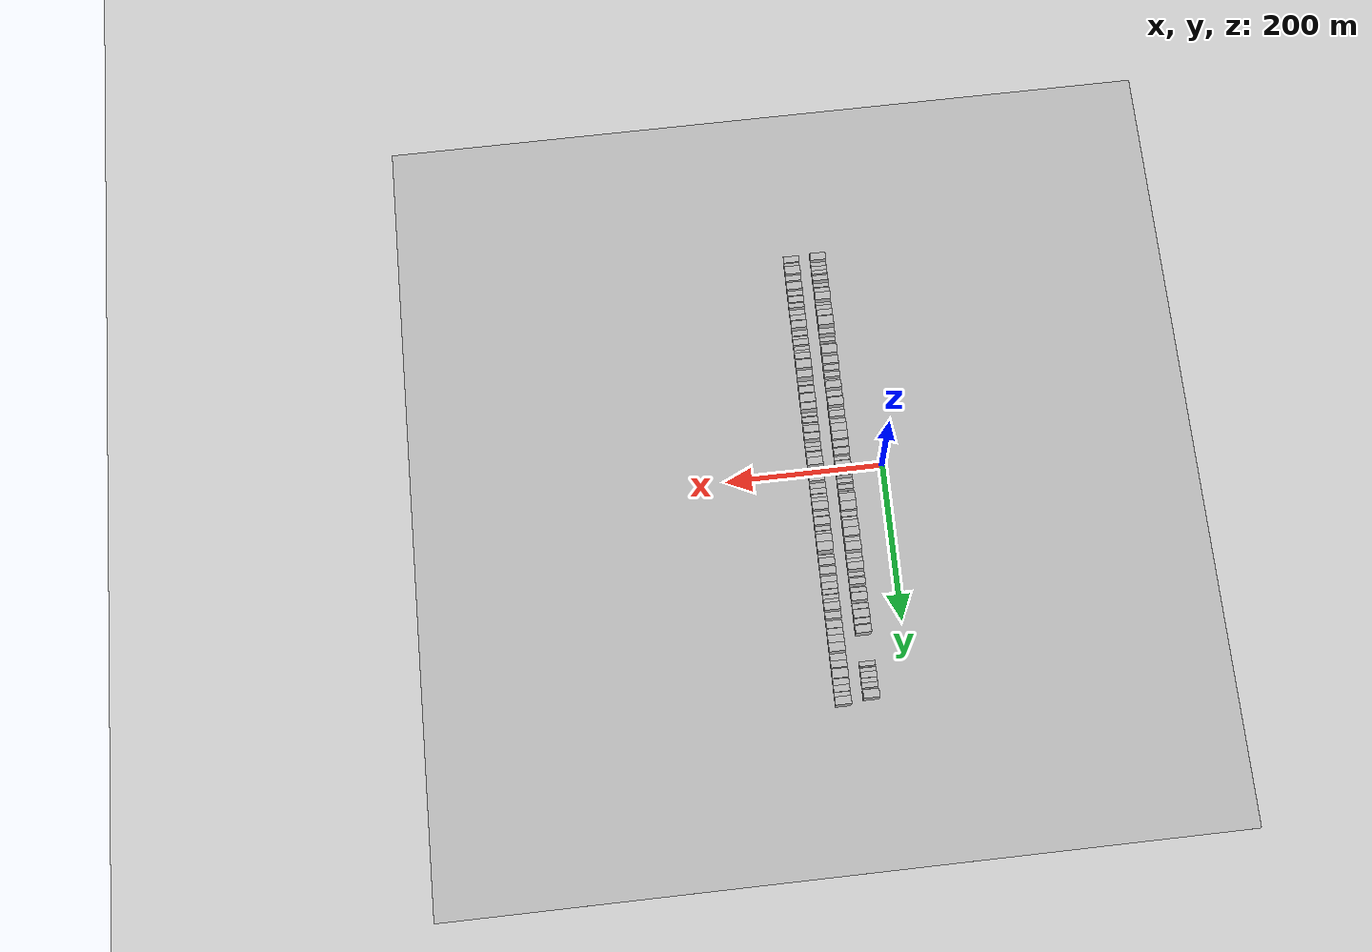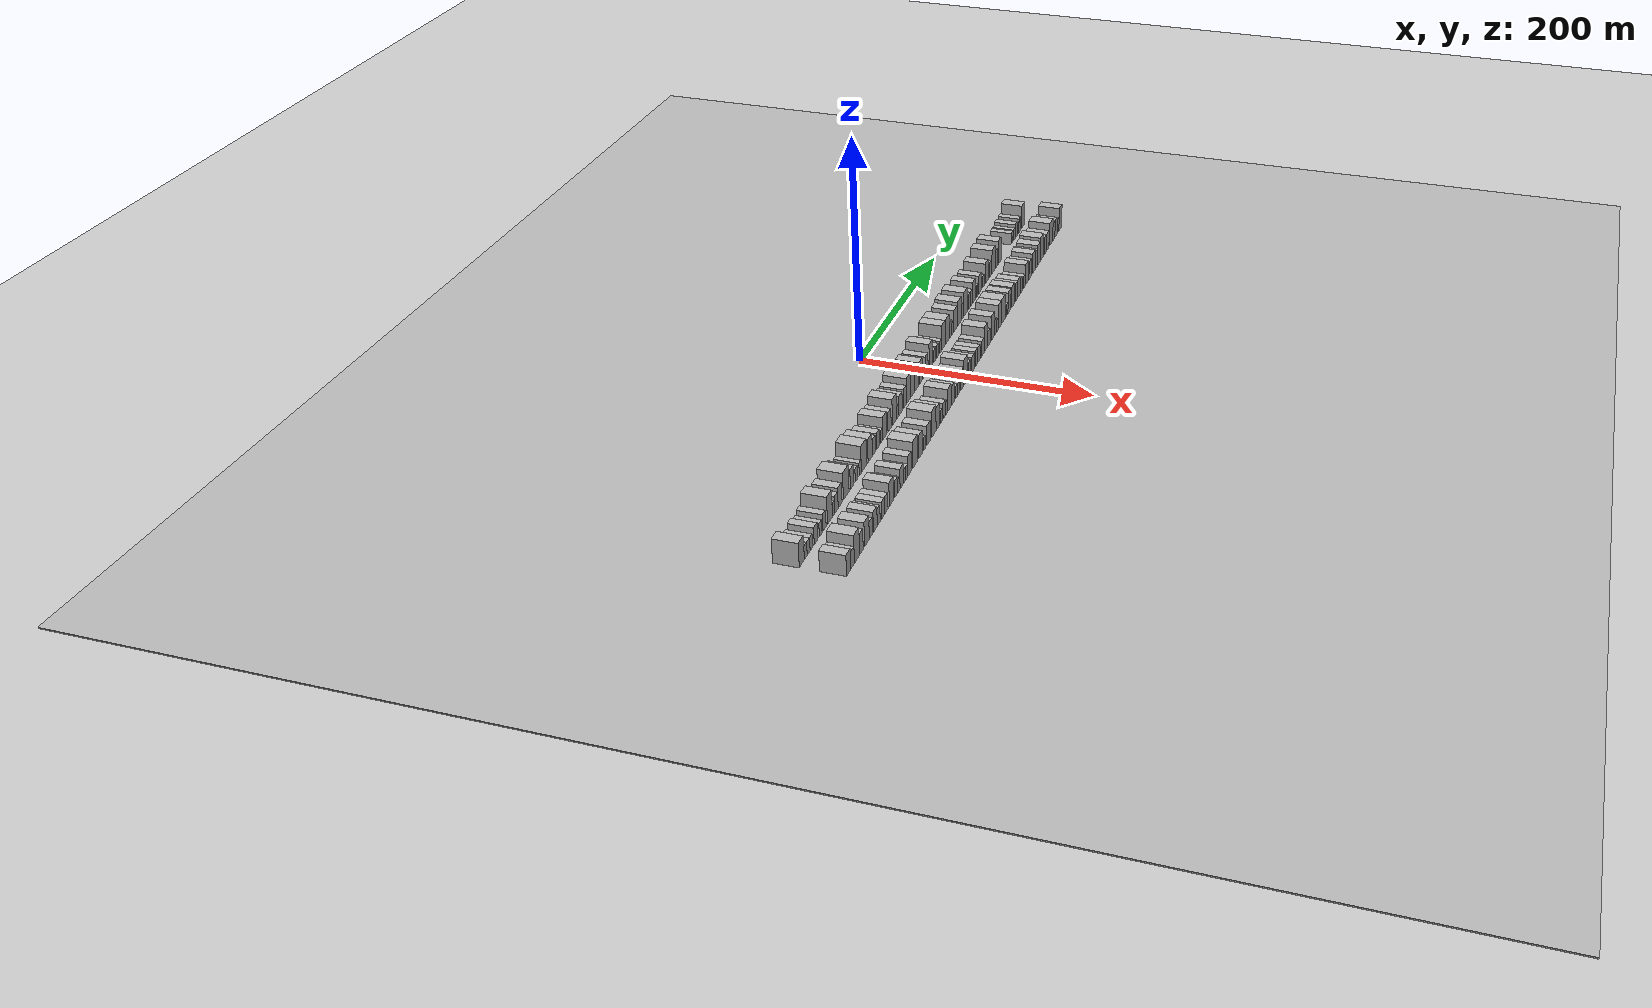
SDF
<?xml version="1.0" encoding="utf-8"?>

<sdf version="1.6">

   <world name="default">

      <gui fullscreen="0">

         <camera name="user_camera">

            <pose>-15 0 4.57585 0 0 0</pose>

            <view_controller>orbit</view_controller>

         </camera>

      </gui>

      <scene>

         <sky>

           <clouds>

             <speed>12</speed>

           </clouds>

         </sky>

         <ambient>0.4 0.4 0.4 1</ambient>

         <background>0.7 0.7 0.7 1</background>

         <shadows>1</shadows>

      </scene>

      <gravity>0 0 -9.8066</gravity>

      <magnetic_field>6e-06 2.3e-05 -4.2e-05</magnetic_field>

      <physics default="0" name="default_physics" type="ode">

         <ode>

            <solver>

               <type>quick</type>

               <iters>10</iters>

               <sor>1.0</sor>

               <use_dynamic_moi_rescaling>0</use_dynamic_moi_rescaling>

            </solver>

            <constraints>

               <cfm>0</cfm>

               <erp>0.2</erp>

               <contact_max_correcting_vel>100</contact_max_correcting_vel>

               <contact_surface_layer>0.001</contact_surface_layer>

            </constraints>

         </ode>

         <max_step_size>0.004</max_step_size>

         <real_time_factor>1</real_time_factor>

         <real_time_update_rate>250</real_time_update_rate>

      </physics>

      <light name="sun" type="directional">

         <cast_shadows>1</cast_shadows>

         <pose>0 0 10 0 0 0</pose>

         <diffuse>0.8 0.8 0.8 1</diffuse>

         <specular>0.2 0.2 0.2 1</specular>

         <attenuation>

            <range>1000</range>

            <constant>0.9</constant>

            <linear>0.01</linear>

            <quadratic>0.001</quadratic>

         </attenuation>

         <direction>-0.5 0.1 -0.9</direction>

      </light>

      <include>

         <name>ground_plane_1</name>

         <uri>model://HANNAS_ground_plane</uri>

         <pose>0 0 0  0 0 0</pose>

      </include>

      <include>

         <name>ground_plane_2</name>

         <uri>model://HANNAS_ground_plane</uri>

         <pose>100 0 0  0 0 0</pose>

      </include>

      <model name="building_1">

         <static>1</static>

         <pose frame="">50.0000 -285.1120 0 0.000000 0.000000 0.000000</pose>

         <link name="link">

            <pose frame="">0 0 10.50 0 0 0</pose>

            <collision name="collision">

               <geometry>

                  <box>

                     <size>20.0000 9.7760 21.0000</size>

                  </box>

               </geometry>

               <max_contacts>10</max_contacts>

               <surface>

                  <contact>

                     <ode/>

                  </contact>

                  <bounce/>

                  <friction>

                     <torsional>

                        <ode/>

                     </torsional>

                     <ode/>

                  </friction>

               </surface>

            </collision>

            <visual name="visual">

               <cast_shadows>0</cast_shadows>

               <geometry>

                  <box>

                     <size>20.0000 9.7760 21.0000</size>

                  </box>

               </geometry>

               <material>

                  <script>

                     <uri>model://HANNAS_wall/materials/scripts</uri>

                     <uri>model://HANNAS_wall/materials/textures</uri>

                     <name>vrc/HANNAS_wall</name>

                  </script>

               </material>

            </visual>

            <self_collide>0</self_collide>

            <enable_wind>0</enable_wind>

            <kinematic>0</kinematic>

         </link>

      </model>

      <model name="building_2">

         <static>1</static>

         <pose frame="">50.0000 -277.5071 0 0.000000 0.000000 0.000000</pose>

         <link name="link">

            <pose frame="">0 0 6.00 0 0 0</pose>

            <collision name="collision">

               <geometry>

                  <box>

                     <size>20.0000 5.4339 12.0000</size>

                  </box>

               </geometry>

               <max_contacts>10</max_contacts>

               <surface>

                  <contact>

                     <ode/>

                  </contact>

                  <bounce/>

                  <friction>

                     <torsional>

                        <ode/>

                     </torsional>

                     <ode/>

                  </friction>

               </surface>

            </collision>

            <visual name="visual">

               <cast_shadows>0</cast_shadows>

               <geometry>

                  <box>

                     <size>20.0000 5.4339 12.0000</size>

                  </box>

               </geometry>

               <material>

                  <script>

                     <uri>model://HANNAS_wall/materials/scripts</uri>

                     <uri>model://HANNAS_wall/materials/textures</uri>

                     <name>vrc/HANNAS_wall</name>

                  </script>

               </material>

            </visual>

            <self_collide>0</self_collide>

            <enable_wind>0</enable_wind>

            <kinematic>0</kinematic>

         </link>

      </model>

      <model name="building_3">

         <static>1</static>

         <pose frame="">50.0000 -271.9558 0 0.000000 0.000000 0.000000</pose>

         <link name="link">

            <pose frame="">0 0 6.00 0 0 0</pose>

            <collision name="collision">

               <geometry>

                  <box>

                     <size>20.0000 5.6687 12.0000</size>

                  </box>

               </geometry>

               <max_contacts>10</max_contacts>

               <surface>

                  <contact>

                     <ode/>

                  </contact>

                  <bounce/>

                  <friction>

                     <torsional>

                        <ode/>

                     </torsional>

                     <ode/>

                  </friction>

               </surface>

            </collision>

            <visual name="visual">

               <cast_shadows>0</cast_shadows>

               <geometry>

                  <box>

                     <size>20.0000 5.6687 12.0000</size>

                  </box>

               </geometry>

               <material>

                  <script>

                     <uri>model://HANNAS_wall/materials/scripts</uri>

                     <uri>model://HANNAS_wall/materials/textures</uri>

                     <name>vrc/HANNAS_wall</name>

                  </script>

               </material>

            </visual>

            <self_collide>0</self_collide>

            <enable_wind>0</enable_wind>

            <kinematic>0</kinematic>

         </link>

      </model>

      <model name="building_4">

         <static>1</static>

         <pose frame="">50.0000 -266.5806 0 0.000000 0.000000 0.000000</pose>

         <link name="link">

            <pose frame="">0 0 6.00 0 0 0</pose>

            <collision name="collision">

               <geometry>

                  <box>

                     <size>20.0000 5.0816 12.0000</size>

                  </box>

               </geometry>

               <max_contacts>10</max_contacts>

               <surface>

                  <contact>

                     <ode/>

                  </contact>

                  <bounce/>

                  <friction>

                     <torsional>

                        <ode/>

                     </torsional>

                     <ode/>

                  </friction>

               </surface>

            </collision>

            <visual name="visual">

               <cast_shadows>0</cast_shadows>

               <geometry>

                  <box>

                     <size>20.0000 5.0816 12.0000</size>

                  </box>

               </geometry>

               <material>

                  <script>

                     <uri>model://HANNAS_wall/materials/scripts</uri>

                     <uri>model://HANNAS_wall/materials/textures</uri>

                     <name>vrc/HANNAS_wall</name>

                  </script>

               </material>

            </visual>

            <self_collide>0</self_collide>

            <enable_wind>0</enable_wind>

            <kinematic>0</kinematic>

         </link>

      </model>

      <model name="building_5">

         <static>1</static>

         <pose frame="">50.0000 -257.4711 0 0.000000 0.000000 0.000000</pose>

         <link name="link">

            <pose frame="">0 0 7.50 0 0 0</pose>

            <collision name="collision">

               <geometry>

                  <box>

                     <size>20.0000 7.1374 15.0000</size>

                  </box>

               </geometry>

               <max_contacts>10</max_contacts>

               <surface>

                  <contact>

                     <ode/>

                  </contact>

                  <bounce/>

                  <friction>

                     <torsional>

                        <ode/>

                     </torsional>

                     <ode/>

                  </friction>

               </surface>

            </collision>

            <visual name="visual">

               <cast_shadows>0</cast_shadows>

               <geometry>

                  <box>

                     <size>20.0000 7.1374 15.0000</size>

                  </box>

               </geometry>

               <material>

                  <script>

                     <uri>model://HANNAS_wall/materials/scripts</uri>

                     <uri>model://HANNAS_wall/materials/textures</uri>

                     <name>vrc/HANNAS_wall</name>

                  </script>

               </material>

            </visual>

            <self_collide>0</self_collide>

            <enable_wind>0</enable_wind>

            <kinematic>0</kinematic>

         </link>

      </model>

      <model name="building_6">

         <static>1</static>

         <pose frame="">50.0000 -248.1935 0 0.000000 0.000000 0.000000</pose>

         <link name="link">

            <pose frame="">0 0 6.00 0 0 0</pose>

            <collision name="collision">

               <geometry>

                  <box>

                     <size>20.0000 5.4177 12.0000</size>

                  </box>

               </geometry>

               <max_contacts>10</max_contacts>

               <surface>

                  <contact>

                     <ode/>

                  </contact>

                  <bounce/>

                  <friction>

                     <torsional>

                        <ode/>

                     </torsional>

                     <ode/>

                  </friction>

               </surface>

            </collision>

            <visual name="visual">

               <cast_shadows>0</cast_shadows>

               <geometry>

                  <box>

                     <size>20.0000 5.4177 12.0000</size>

                  </box>

               </geometry>

               <material>

                  <script>

                     <uri>model://HANNAS_wall/materials/scripts</uri>

                     <uri>model://HANNAS_wall/materials/textures</uri>

                     <name>vrc/HANNAS_wall</name>

                  </script>

               </material>

            </visual>

            <self_collide>0</self_collide>

            <enable_wind>0</enable_wind>

            <kinematic>0</kinematic>

         </link>

      </model>

      <model name="building_7">

         <static>1</static>

         <pose frame="">50.0000 -240.3888 0 0.000000 0.000000 0.000000</pose>

         <link name="link">

            <pose frame="">0 0 7.50 0 0 0</pose>

            <collision name="collision">

               <geometry>

                  <box>

                     <size>20.0000 6.1917 15.0000</size>

                  </box>

               </geometry>

               <max_contacts>10</max_contacts>

               <surface>

                  <contact>

                     <ode/>

                  </contact>

                  <bounce/>

                  <friction>

                     <torsional>

                        <ode/>

                     </torsional>

                     <ode/>

                  </friction>

               </surface>

            </collision>

            <visual name="visual">

               <cast_shadows>0</cast_shadows>

               <geometry>

                  <box>

                     <size>20.0000 6.1917 15.0000</size>

                  </box>

               </geometry>

               <material>

                  <script>

                     <uri>model://HANNAS_wall/materials/scripts</uri>

                     <uri>model://HANNAS_wall/materials/textures</uri>

                     <name>vrc/HANNAS_wall</name>

                  </script>

               </material>

            </visual>

            <self_collide>0</self_collide>

            <enable_wind>0</enable_wind>

            <kinematic>0</kinematic>

         </link>

      </model>

      <model name="building_8">

         <static>1</static>

         <pose frame="">50.0000 -229.2782 0 0.000000 0.000000 0.000000</pose>

         <link name="link">

            <pose frame="">0 0 12.00 0 0 0</pose>

            <collision name="collision">

               <geometry>

                  <box>

                     <size>20.0000 10.0295 24.0000</size>

                  </box>

               </geometry>

               <max_contacts>10</max_contacts>

               <surface>

                  <contact>

                     <ode/>

                  </contact>

                  <bounce/>

                  <friction>

                     <torsional>

                        <ode/>

                     </torsional>

                     <ode/>

                  </friction>

               </surface>

            </collision>

            <visual name="visual">

               <cast_shadows>0</cast_shadows>

               <geometry>

                  <box>

                     <size>20.0000 10.0295 24.0000</size>

                  </box>

               </geometry>

               <material>

                  <script>

                     <uri>model://HANNAS_wall/materials/scripts</uri>

                     <uri>model://HANNAS_wall/materials/textures</uri>

                     <name>vrc/HANNAS_wall</name>

                  </script>

               </material>

            </visual>

            <self_collide>0</self_collide>

            <enable_wind>0</enable_wind>

            <kinematic>0</kinematic>

         </link>

      </model>

      <model name="building_9">

         <static>1</static>

         <pose frame="">50.0000 -221.8619 0 0.000000 0.000000 0.000000</pose>

         <link name="link">

            <pose frame="">0 0 6.00 0 0 0</pose>

            <collision name="collision">

               <geometry>

                  <box>

                     <size>20.0000 4.8031 12.0000</size>

                  </box>

               </geometry>

               <max_contacts>10</max_contacts>

               <surface>

                  <contact>

                     <ode/>

                  </contact>

                  <bounce/>

                  <friction>

                     <torsional>

                        <ode/>

                     </torsional>

                     <ode/>

                  </friction>

               </surface>

            </collision>

            <visual name="visual">

               <cast_shadows>0</cast_shadows>

               <geometry>

                  <box>

                     <size>20.0000 4.8031 12.0000</size>

                  </box>

               </geometry>

               <material>

                  <script>

                     <uri>model://HANNAS_wall/materials/scripts</uri>

                     <uri>model://HANNAS_wall/materials/textures</uri>

                     <name>vrc/HANNAS_wall</name>

                  </script>

               </material>

            </visual>

            <self_collide>0</self_collide>

            <enable_wind>0</enable_wind>

            <kinematic>0</kinematic>

         </link>

      </model>

      <model name="building_10">

         <static>1</static>

         <pose frame="">50.0000 -215.8952 0 0.000000 0.000000 0.000000</pose>

         <link name="link">

            <pose frame="">0 0 7.50 0 0 0</pose>

            <collision name="collision">

               <geometry>

                  <box>

                     <size>20.0000 7.1303 15.0000</size>

                  </box>

               </geometry>

               <max_contacts>10</max_contacts>

               <surface>

                  <contact>

                     <ode/>

                  </contact>

                  <bounce/>

                  <friction>

                     <torsional>

                        <ode/>

                     </torsional>

                     <ode/>

                  </friction>

               </surface>

            </collision>

            <visual name="visual">

               <cast_shadows>0</cast_shadows>

               <geometry>

                  <box>

                     <size>20.0000 7.1303 15.0000</size>

                  </box>

               </geometry>

               <material>

                  <script>

                     <uri>model://HANNAS_wall/materials/scripts</uri>

                     <uri>model://HANNAS_wall/materials/textures</uri>

                     <name>vrc/HANNAS_wall</name>

                  </script>

               </material>

            </visual>

            <self_collide>0</self_collide>

            <enable_wind>0</enable_wind>

            <kinematic>0</kinematic>

         </link>

      </model>

      <model name="building_11">

         <static>1</static>

         <pose frame="">50.0000 -208.3182 0 0.000000 0.000000 0.000000</pose>

         <link name="link">

            <pose frame="">0 0 9.00 0 0 0</pose>

            <collision name="collision">

               <geometry>

                  <box>

                     <size>20.0000 8.0237 18.0000</size>

                  </box>

               </geometry>

               <max_contacts>10</max_contacts>

               <surface>

                  <contact>

                     <ode/>

                  </contact>

                  <bounce/>

                  <friction>

                     <torsional>

                        <ode/>

                     </torsional>

                     <ode/>

                  </friction>

               </surface>

            </collision>

            <visual name="visual">

               <cast_shadows>0</cast_shadows>

               <geometry>

                  <box>

                     <size>20.0000 8.0237 18.0000</size>

                  </box>

               </geometry>

               <material>

                  <script>

                     <uri>model://HANNAS_wall/materials/scripts</uri>

                     <uri>model://HANNAS_wall/materials/textures</uri>

                     <name>vrc/HANNAS_wall</name>

                  </script>

               </material>

            </visual>

            <self_collide>0</self_collide>

            <enable_wind>0</enable_wind>

            <kinematic>0</kinematic>

         </link>

      </model>

      <model name="building_12">

         <static>1</static>

         <pose frame="">50.0000 -195.3525 0 0.000000 0.000000 0.000000</pose>

         <link name="link">

            <pose frame="">0 0 12.00 0 0 0</pose>

            <collision name="collision">

               <geometry>

                  <box>

                     <size>20.0000 11.9077 24.0000</size>

                  </box>

               </geometry>

               <max_contacts>10</max_contacts>

               <surface>

                  <contact>

                     <ode/>

                  </contact>

                  <bounce/>

                  <friction>

                     <torsional>

                        <ode/>

                     </torsional>

                     <ode/>

                  </friction>

               </surface>

            </collision>

            <visual name="visual">

               <cast_shadows>0</cast_shadows>

               <geometry>

                  <box>

                     <size>20.0000 11.9077 24.0000</size>

                  </box>

               </geometry>

               <material>

                  <script>

                     <uri>model://HANNAS_wall/materials/scripts</uri>

                     <uri>model://HANNAS_wall/materials/textures</uri>

                     <name>vrc/HANNAS_wall</name>

                  </script>

               </material>

            </visual>

            <self_collide>0</self_collide>

            <enable_wind>0</enable_wind>

            <kinematic>0</kinematic>

         </link>

      </model>

      <model name="building_13">

         <static>1</static>

         <pose frame="">50.0000 -182.7060 0 0.000000 0.000000 0.000000</pose>

         <link name="link">

            <pose frame="">0 0 9.00 0 0 0</pose>

            <collision name="collision">

               <geometry>

                  <box>

                     <size>20.0000 7.3852 18.0000</size>

                  </box>

               </geometry>

               <max_contacts>10</max_contacts>

               <surface>

                  <contact>

                     <ode/>

                  </contact>

                  <bounce/>

                  <friction>

                     <torsional>

                        <ode/>

                     </torsional>

                     <ode/>

                  </friction>

               </surface>

            </collision>

            <visual name="visual">

               <cast_shadows>0</cast_shadows>

               <geometry>

                  <box>

                     <size>20.0000 7.3852 18.0000</size>

                  </box>

               </geometry>

               <material>

                  <script>

                     <uri>model://HANNAS_wall/materials/scripts</uri>

                     <uri>model://HANNAS_wall/materials/textures</uri>

                     <name>vrc/HANNAS_wall</name>

                  </script>

               </material>

            </visual>

            <self_collide>0</self_collide>

            <enable_wind>0</enable_wind>

            <kinematic>0</kinematic>

         </link>

      </model>

      <model name="building_14">

         <static>1</static>

         <pose frame="">50.0000 -173.1406 0 0.000000 0.000000 0.000000</pose>

         <link name="link">

            <pose frame="">0 0 6.00 0 0 0</pose>

            <collision name="collision">

               <geometry>

                  <box>

                     <size>20.0000 5.7456 12.0000</size>

                  </box>

               </geometry>

               <max_contacts>10</max_contacts>

               <surface>

                  <contact>

                     <ode/>

                  </contact>

                  <bounce/>

                  <friction>

                     <torsional>

                        <ode/>

                     </torsional>

                     <ode/>

                  </friction>

               </surface>

            </collision>

            <visual name="visual">

               <cast_shadows>0</cast_shadows>

               <geometry>

                  <box>

                     <size>20.0000 5.7456 12.0000</size>

                  </box>

               </geometry>

               <material>

                  <script>

                     <uri>model://HANNAS_wall/materials/scripts</uri>

                     <uri>model://HANNAS_wall/materials/textures</uri>

                     <name>vrc/HANNAS_wall</name>

                  </script>

               </material>

            </visual>

            <self_collide>0</self_collide>

            <enable_wind>0</enable_wind>

            <kinematic>0</kinematic>

         </link>

      </model>

      <model name="building_15">

         <static>1</static>

         <pose frame="">50.0000 -164.8532 0 0.000000 0.000000 0.000000</pose>

         <link name="link">

            <pose frame="">0 0 6.00 0 0 0</pose>

            <collision name="collision">

               <geometry>

                  <box>

                     <size>20.0000 4.8292 12.0000</size>

                  </box>

               </geometry>

               <max_contacts>10</max_contacts>

               <surface>

                  <contact>

                     <ode/>

                  </contact>

                  <bounce/>

                  <friction>

                     <torsional>

                        <ode/>

                     </torsional>

                     <ode/>

                  </friction>

               </surface>

            </collision>

            <visual name="visual">

               <cast_shadows>0</cast_shadows>

               <geometry>

                  <box>

                     <size>20.0000 4.8292 12.0000</size>

                  </box>

               </geometry>

               <material>

                  <script>

                     <uri>model://HANNAS_wall/materials/scripts</uri>

                     <uri>model://HANNAS_wall/materials/textures</uri>

                     <name>vrc/HANNAS_wall</name>

                  </script>

               </material>

            </visual>

            <self_collide>0</self_collide>

            <enable_wind>0</enable_wind>

            <kinematic>0</kinematic>

         </link>

      </model>

      <model name="building_16">

         <static>1</static>

         <pose frame="">50.0000 -156.5043 0 0.000000 0.000000 0.000000</pose>

         <link name="link">

            <pose frame="">0 0 12.00 0 0 0</pose>

            <collision name="collision">

               <geometry>

                  <box>

                     <size>20.0000 11.8687 24.0000</size>

                  </box>

               </geometry>

               <max_contacts>10</max_contacts>

               <surface>

                  <contact>

                     <ode/>

                  </contact>

                  <bounce/>

                  <friction>

                     <torsional>

                        <ode/>

                     </torsional>

                     <ode/>

                  </friction>

               </surface>

            </collision>

            <visual name="visual">

               <cast_shadows>0</cast_shadows>

               <geometry>

                  <box>

                     <size>20.0000 11.8687 24.0000</size>

                  </box>

               </geometry>

               <material>

                  <script>

                     <uri>model://HANNAS_wall/materials/scripts</uri>

                     <uri>model://HANNAS_wall/materials/textures</uri>

                     <name>vrc/HANNAS_wall</name>

                  </script>

               </material>

            </visual>

            <self_collide>0</self_collide>

            <enable_wind>0</enable_wind>

            <kinematic>0</kinematic>

         </link>

      </model>

      <model name="building_17">

         <static>1</static>

         <pose frame="">50.0000 -142.6016 0 0.000000 0.000000 0.000000</pose>

         <link name="link">

            <pose frame="">0 0 10.50 0 0 0</pose>

            <collision name="collision">

               <geometry>

                  <box>

                     <size>20.0000 9.9367 21.0000</size>

                  </box>

               </geometry>

               <max_contacts>10</max_contacts>

               <surface>

                  <contact>

                     <ode/>

                  </contact>

                  <bounce/>

                  <friction>

                     <torsional>

                        <ode/>

                     </torsional>

                     <ode/>

                  </friction>

               </surface>

            </collision>

            <visual name="visual">

               <cast_shadows>0</cast_shadows>

               <geometry>

                  <box>

                     <size>20.0000 9.9367 21.0000</size>

                  </box>

               </geometry>

               <material>

                  <script>

                     <uri>model://HANNAS_wall/materials/scripts</uri>

                     <uri>model://HANNAS_wall/materials/textures</uri>

                     <name>vrc/HANNAS_wall</name>

                  </script>

               </material>

            </visual>

            <self_collide>0</self_collide>

            <enable_wind>0</enable_wind>

            <kinematic>0</kinematic>

         </link>

      </model>

      <model name="building_18">

         <static>1</static>

         <pose frame="">50.0000 -133.8957 0 0.000000 0.000000 0.000000</pose>

         <link name="link">

            <pose frame="">0 0 7.50 0 0 0</pose>

            <collision name="collision">

               <geometry>

                  <box>

                     <size>20.0000 7.4753 15.0000</size>

                  </box>

               </geometry>

               <max_contacts>10</max_contacts>

               <surface>

                  <contact>

                     <ode/>

                  </contact>

                  <bounce/>

                  <friction>

                     <torsional>

                        <ode/>

                     </torsional>

                     <ode/>

                  </friction>

               </surface>

            </collision>

            <visual name="visual">

               <cast_shadows>0</cast_shadows>

               <geometry>

                  <box>

                     <size>20.0000 7.4753 15.0000</size>

                  </box>

               </geometry>

               <material>

                  <script>

                     <uri>model://HANNAS_wall/materials/scripts</uri>

                     <uri>model://HANNAS_wall/materials/textures</uri>

                     <name>vrc/HANNAS_wall</name>

                  </script>

               </material>

            </visual>

            <self_collide>0</self_collide>

            <enable_wind>0</enable_wind>

            <kinematic>0</kinematic>

         </link>

      </model>

      <model name="building_19">

         <static>1</static>

         <pose frame="">50.0000 -124.5786 0 0.000000 0.000000 0.000000</pose>

         <link name="link">

            <pose frame="">0 0 7.50 0 0 0</pose>

            <collision name="collision">

               <geometry>

                  <box>

                     <size>20.0000 7.1588 15.0000</size>

                  </box>

               </geometry>

               <max_contacts>10</max_contacts>

               <surface>

                  <contact>

                     <ode/>

                  </contact>

                  <bounce/>

                  <friction>

                     <torsional>

                        <ode/>

                     </torsional>

                     <ode/>

                  </friction>

               </surface>

            </collision>

            <visual name="visual">

               <cast_shadows>0</cast_shadows>

               <geometry>

                  <box>

                     <size>20.0000 7.1588 15.0000</size>

                  </box>

               </geometry>

               <material>

                  <script>

                     <uri>model://HANNAS_wall/materials/scripts</uri>

                     <uri>model://HANNAS_wall/materials/textures</uri>

                     <name>vrc/HANNAS_wall</name>

                  </script>

               </material>

            </visual>

            <self_collide>0</self_collide>

            <enable_wind>0</enable_wind>

            <kinematic>0</kinematic>

         </link>

      </model>

      <model name="building_20">

         <static>1</static>

         <pose frame="">50.0000 -116.4364 0 0.000000 0.000000 0.000000</pose>

         <link name="link">

            <pose frame="">0 0 6.00 0 0 0</pose>

            <collision name="collision">

               <geometry>

                  <box>

                     <size>20.0000 5.1256 12.0000</size>

                  </box>

               </geometry>

               <max_contacts>10</max_contacts>

               <surface>

                  <contact>

                     <ode/>

                  </contact>

                  <bounce/>

                  <friction>

                     <torsional>

                        <ode/>

                     </torsional>

                     <ode/>

                  </friction>

               </surface>

            </collision>

            <visual name="visual">

               <cast_shadows>0</cast_shadows>

               <geometry>

                  <box>

                     <size>20.0000 5.1256 12.0000</size>

                  </box>

               </geometry>

               <material>

                  <script>

                     <uri>model://HANNAS_wall/materials/scripts</uri>

                     <uri>model://HANNAS_wall/materials/textures</uri>

                     <name>vrc/HANNAS_wall</name>

                  </script>

               </material>

            </visual>

            <self_collide>0</self_collide>

            <enable_wind>0</enable_wind>

            <kinematic>0</kinematic>

         </link>

      </model>

      <model name="building_21">

         <static>1</static>

         <pose frame="">50.0000 -109.1914 0 0.000000 0.000000 0.000000</pose>

         <link name="link">

            <pose frame="">0 0 10.50 0 0 0</pose>

            <collision name="collision">

               <geometry>

                  <box>

                     <size>20.0000 9.3645 21.0000</size>

                  </box>

               </geometry>

               <max_contacts>10</max_contacts>

               <surface>

                  <contact>

                     <ode/>

                  </contact>

                  <bounce/>

                  <friction>

                     <torsional>

                        <ode/>

                     </torsional>

                     <ode/>

                  </friction>

               </surface>

            </collision>

            <visual name="visual">

               <cast_shadows>0</cast_shadows>

               <geometry>

                  <box>

                     <size>20.0000 9.3645 21.0000</size>

                  </box>

               </geometry>

               <material>

                  <script>

                     <uri>model://HANNAS_wall/materials/scripts</uri>

                     <uri>model://HANNAS_wall/materials/textures</uri>

                     <name>vrc/HANNAS_wall</name>

                  </script>

               </material>

            </visual>

            <self_collide>0</self_collide>

            <enable_wind>0</enable_wind>

            <kinematic>0</kinematic>

         </link>

      </model>

      <model name="building_22">

         <static>1</static>

         <pose frame="">50.0000 -97.6851 0 0.000000 0.000000 0.000000</pose>

         <link name="link">

            <pose frame="">0 0 9.00 0 0 0</pose>

            <collision name="collision">

               <geometry>

                  <box>

                     <size>20.0000 7.6480 18.0000</size>

                  </box>

               </geometry>

               <max_contacts>10</max_contacts>

               <surface>

                  <contact>

                     <ode/>

                  </contact>

                  <bounce/>

                  <friction>

                     <torsional>

                        <ode/>

                     </torsional>

                     <ode/>

                  </friction>

               </surface>

            </collision>

            <visual name="visual">

               <cast_shadows>0</cast_shadows>

               <geometry>

                  <box>

                     <size>20.0000 7.6480 18.0000</size>

                  </box>

               </geometry>

               <material>

                  <script>

                     <uri>model://HANNAS_wall/materials/scripts</uri>

                     <uri>model://HANNAS_wall/materials/textures</uri>

                     <name>vrc/HANNAS_wall</name>

                  </script>

               </material>

            </visual>

            <self_collide>0</self_collide>

            <enable_wind>0</enable_wind>

            <kinematic>0</kinematic>

         </link>

      </model>

      <model name="building_23">

         <static>1</static>

         <pose frame="">50.0000 -85.6363 0 0.000000 0.000000 0.000000</pose>

         <link name="link">

            <pose frame="">0 0 12.00 0 0 0</pose>

            <collision name="collision">

               <geometry>

                  <box>

                     <size>20.0000 10.4497 24.0000</size>

                  </box>

               </geometry>

               <max_contacts>10</max_contacts>

               <surface>

                  <contact>

                     <ode/>

                  </contact>

                  <bounce/>

                  <friction>

                     <torsional>

                        <ode/>

                     </torsional>

                     <ode/>

                  </friction>

               </surface>

            </collision>

            <visual name="visual">

               <cast_shadows>0</cast_shadows>

               <geometry>

                  <box>

                     <size>20.0000 10.4497 24.0000</size>

                  </box>

               </geometry>

               <material>

                  <script>

                     <uri>model://HANNAS_wall/materials/scripts</uri>

                     <uri>model://HANNAS_wall/materials/textures</uri>

                     <name>vrc/HANNAS_wall</name>

                  </script>

               </material>

            </visual>

            <self_collide>0</self_collide>

            <enable_wind>0</enable_wind>

            <kinematic>0</kinematic>

         </link>

      </model>

      <model name="building_24">

         <static>1</static>

         <pose frame="">50.0000 -77.7396 0 0.000000 0.000000 0.000000</pose>

         <link name="link">

            <pose frame="">0 0 6.00 0 0 0</pose>

            <collision name="collision">

               <geometry>

                  <box>

                     <size>20.0000 5.3436 12.0000</size>

                  </box>

               </geometry>

               <max_contacts>10</max_contacts>

               <surface>

                  <contact>

                     <ode/>

                  </contact>

                  <bounce/>

                  <friction>

                     <torsional>

                        <ode/>

                     </torsional>

                     <ode/>

                  </friction>

               </surface>

            </collision>

            <visual name="visual">

               <cast_shadows>0</cast_shadows>

               <geometry>

                  <box>

                     <size>20.0000 5.3436 12.0000</size>

                  </box>

               </geometry>

               <material>

                  <script>

                     <uri>model://HANNAS_wall/materials/scripts</uri>

                     <uri>model://HANNAS_wall/materials/textures</uri>

                     <name>vrc/HANNAS_wall</name>

                  </script>

               </material>

            </visual>

            <self_collide>0</self_collide>

            <enable_wind>0</enable_wind>

            <kinematic>0</kinematic>

         </link>

      </model>

      <model name="building_25">

         <static>1</static>

         <pose frame="">50.0000 -70.9836 0 0.000000 0.000000 0.000000</pose>

         <link name="link">

            <pose frame="">0 0 9.00 0 0 0</pose>

            <collision name="collision">

               <geometry>

                  <box>

                     <size>20.0000 8.1685 18.0000</size>

                  </box>

               </geometry>

               <max_contacts>10</max_contacts>

               <surface>

                  <contact>

                     <ode/>

                  </contact>

                  <bounce/>

                  <friction>

                     <torsional>

                        <ode/>

                     </torsional>

                     <ode/>

                  </friction>

               </surface>

            </collision>

            <visual name="visual">

               <cast_shadows>0</cast_shadows>

               <geometry>

                  <box>

                     <size>20.0000 8.1685 18.0000</size>

                  </box>

               </geometry>

               <material>

                  <script>

                     <uri>model://HANNAS_wall/materials/scripts</uri>

                     <uri>model://HANNAS_wall/materials/textures</uri>

                     <name>vrc/HANNAS_wall</name>

                  </script>

               </material>

            </visual>

            <self_collide>0</self_collide>

            <enable_wind>0</enable_wind>

            <kinematic>0</kinematic>

         </link>

      </model>

      <model name="building_26">

         <static>1</static>

         <pose frame="">50.0000 -60.1290 0 0.000000 0.000000 0.000000</pose>

         <link name="link">

            <pose frame="">0 0 9.00 0 0 0</pose>

            <collision name="collision">

               <geometry>

                  <box>

                     <size>20.0000 7.5406 18.0000</size>

                  </box>

               </geometry>

               <max_contacts>10</max_contacts>

               <surface>

                  <contact>

                     <ode/>

                  </contact>

                  <bounce/>

                  <friction>

                     <torsional>

                        <ode/>

                     </torsional>

                     <ode/>

                  </friction>

               </surface>

            </collision>

            <visual name="visual">

               <cast_shadows>0</cast_shadows>

               <geometry>

                  <box>

                     <size>20.0000 7.5406 18.0000</size>

                  </box>

               </geometry>

               <material>

                  <script>

                     <uri>model://HANNAS_wall/materials/scripts</uri>

                     <uri>model://HANNAS_wall/materials/textures</uri>

                     <name>vrc/HANNAS_wall</name>

                  </script>

               </material>

            </visual>

            <self_collide>0</self_collide>

            <enable_wind>0</enable_wind>

            <kinematic>0</kinematic>

         </link>

      </model>

      <model name="building_27">

         <static>1</static>

         <pose frame="">50.0000 -51.2133 0 0.000000 0.000000 0.000000</pose>

         <link name="link">

            <pose frame="">0 0 12.00 0 0 0</pose>

            <collision name="collision">

               <geometry>

                  <box>

                     <size>20.0000 10.2908 24.0000</size>

                  </box>

               </geometry>

               <max_contacts>10</max_contacts>

               <surface>

                  <contact>

                     <ode/>

                  </contact>

                  <bounce/>

                  <friction>

                     <torsional>

                        <ode/>

                     </torsional>

                     <ode/>

                  </friction>

               </surface>

            </collision>

            <visual name="visual">

               <cast_shadows>0</cast_shadows>

               <geometry>

                  <box>

                     <size>20.0000 10.2908 24.0000</size>

                  </box>

               </geometry>

               <material>

                  <script>

                     <uri>model://HANNAS_wall/materials/scripts</uri>

                     <uri>model://HANNAS_wall/materials/textures</uri>

                     <name>vrc/HANNAS_wall</name>

                  </script>

               </material>

            </visual>

            <self_collide>0</self_collide>

            <enable_wind>0</enable_wind>

            <kinematic>0</kinematic>

         </link>

      </model>

      <model name="building_28">

         <static>1</static>

         <pose frame="">50.0000 -40.7149 0 0.000000 0.000000 0.000000</pose>

         <link name="link">

            <pose frame="">0 0 12.00 0 0 0</pose>

            <collision name="collision">

               <geometry>

                  <box>

                     <size>20.0000 10.7061 24.0000</size>

                  </box>

               </geometry>

               <max_contacts>10</max_contacts>

               <surface>

                  <contact>

                     <ode/>

                  </contact>

                  <bounce/>

                  <friction>

                     <torsional>

                        <ode/>

                     </torsional>

                     <ode/>

                  </friction>

               </surface>

            </collision>

            <visual name="visual">

               <cast_shadows>0</cast_shadows>

               <geometry>

                  <box>

                     <size>20.0000 10.7061 24.0000</size>

                  </box>

               </geometry>

               <material>

                  <script>

                     <uri>model://HANNAS_wall/materials/scripts</uri>

                     <uri>model://HANNAS_wall/materials/textures</uri>

                     <name>vrc/HANNAS_wall</name>

                  </script>

               </material>

            </visual>

            <self_collide>0</self_collide>

            <enable_wind>0</enable_wind>

            <kinematic>0</kinematic>

         </link>

      </model>

      <model name="building_29">

         <static>1</static>

         <pose frame="">50.0000 -30.9056 0 0.000000 0.000000 0.000000</pose>

         <link name="link">

            <pose frame="">0 0 9.00 0 0 0</pose>

            <collision name="collision">

               <geometry>

                  <box>

                     <size>20.0000 8.9124 18.0000</size>

                  </box>

               </geometry>

               <max_contacts>10</max_contacts>

               <surface>

                  <contact>

                     <ode/>

                  </contact>

                  <bounce/>

                  <friction>

                     <torsional>

                        <ode/>

                     </torsional>

                     <ode/>

                  </friction>

               </surface>

            </collision>

            <visual name="visual">

               <cast_shadows>0</cast_shadows>

               <geometry>

                  <box>

                     <size>20.0000 8.9124 18.0000</size>

                  </box>

               </geometry>

               <material>

                  <script>

                     <uri>model://HANNAS_wall/materials/scripts</uri>

                     <uri>model://HANNAS_wall/materials/textures</uri>

                     <name>vrc/HANNAS_wall</name>

                  </script>

               </material>

            </visual>

            <self_collide>0</self_collide>

            <enable_wind>0</enable_wind>

            <kinematic>0</kinematic>

         </link>

      </model>

      <model name="building_30">

         <static>1</static>

         <pose frame="">50.0000 -20.0136 0 0.000000 0.000000 0.000000</pose>

         <link name="link">

            <pose frame="">0 0 10.50 0 0 0</pose>

            <collision name="collision">

               <geometry>

                  <box>

                     <size>20.0000 8.8717 21.0000</size>

                  </box>

               </geometry>

               <max_contacts>10</max_contacts>

               <surface>

                  <contact>

                     <ode/>

                  </contact>

                  <bounce/>

                  <friction>

                     <torsional>

                        <ode/>

                     </torsional>

                     <ode/>

                  </friction>

               </surface>

            </collision>

            <visual name="visual">

               <cast_shadows>0</cast_shadows>

               <geometry>

                  <box>

                     <size>20.0000 8.8717 21.0000</size>

                  </box>

               </geometry>

               <material>

                  <script>

                     <uri>model://HANNAS_wall/materials/scripts</uri>

                     <uri>model://HANNAS_wall/materials/textures</uri>

                     <name>vrc/HANNAS_wall</name>

                  </script>

               </material>

            </visual>

            <self_collide>0</self_collide>

            <enable_wind>0</enable_wind>

            <kinematic>0</kinematic>

         </link>

      </model>

      <model name="building_31">

         <static>1</static>

         <pose frame="">50.0000 -12.9864 0 0.000000 0.000000 0.000000</pose>

         <link name="link">

            <pose frame="">0 0 6.00 0 0 0</pose>

            <collision name="collision">

               <geometry>

                  <box>

                     <size>20.0000 5.1826 12.0000</size>

                  </box>

               </geometry>

               <max_contacts>10</max_contacts>

               <surface>

                  <contact>

                     <ode/>

                  </contact>

                  <bounce/>

                  <friction>

                     <torsional>

                        <ode/>

                     </torsional>

                     <ode/>

                  </friction>

               </surface>

            </collision>

            <visual name="visual">

               <cast_shadows>0</cast_shadows>

               <geometry>

                  <box>

                     <size>20.0000 5.1826 12.0000</size>

                  </box>

               </geometry>

               <material>

                  <script>

                     <uri>model://HANNAS_wall/materials/scripts</uri>

                     <uri>model://HANNAS_wall/materials/textures</uri>

                     <name>vrc/HANNAS_wall</name>

                  </script>

               </material>

            </visual>

            <self_collide>0</self_collide>

            <enable_wind>0</enable_wind>

            <kinematic>0</kinematic>

         </link>

      </model>

      <model name="building_32">

         <static>1</static>

         <pose frame="">50.0000 -4.6984 0 0.000000 0.000000 0.000000</pose>

         <link name="link">

            <pose frame="">0 0 9.00 0 0 0</pose>

            <collision name="collision">

               <geometry>

                  <box>

                     <size>20.0000 7.3933 18.0000</size>

                  </box>

               </geometry>

               <max_contacts>10</max_contacts>

               <surface>

                  <contact>

                     <ode/>

                  </contact>

                  <bounce/>

                  <friction>

                     <torsional>

                        <ode/>

                     </torsional>

                     <ode/>

                  </friction>

               </surface>

            </collision>

            <visual name="visual">

               <cast_shadows>0</cast_shadows>

               <geometry>

                  <box>

                     <size>20.0000 7.3933 18.0000</size>

                  </box>

               </geometry>

               <material>

                  <script>

                     <uri>model://HANNAS_wall/materials/scripts</uri>

                     <uri>model://HANNAS_wall/materials/textures</uri>

                     <name>vrc/HANNAS_wall</name>

                  </script>

               </material>

            </visual>

            <self_collide>0</self_collide>

            <enable_wind>0</enable_wind>

            <kinematic>0</kinematic>

         </link>

      </model>

      <model name="building_33">

         <static>1</static>

         <pose frame="">50.0000 6.8137 0 0.000000 0.000000 0.000000</pose>

         <link name="link">

            <pose frame="">0 0 12.00 0 0 0</pose>

            <collision name="collision">

               <geometry>

                  <box>

                     <size>20.0000 9.6309 24.0000</size>

                  </box>

               </geometry>

               <max_contacts>10</max_contacts>

               <surface>

                  <contact>

                     <ode/>

                  </contact>

                  <bounce/>

                  <friction>

                     <torsional>

                        <ode/>

                     </torsional>

                     <ode/>

                  </friction>

               </surface>

            </collision>

            <visual name="visual">

               <cast_shadows>0</cast_shadows>

               <geometry>

                  <box>

                     <size>20.0000 9.6309 24.0000</size>

                  </box>

               </geometry>

               <material>

                  <script>

                     <uri>model://HANNAS_wall/materials/scripts</uri>

                     <uri>model://HANNAS_wall/materials/textures</uri>

                     <name>vrc/HANNAS_wall</name>

                  </script>

               </material>

            </visual>

            <self_collide>0</self_collide>

            <enable_wind>0</enable_wind>

            <kinematic>0</kinematic>

         </link>

      </model>

      <model name="building_34">

         <static>1</static>

         <pose frame="">50.0000 16.5989 0 0.000000 0.000000 0.000000</pose>

         <link name="link">

            <pose frame="">0 0 6.00 0 0 0</pose>

            <collision name="collision">

               <geometry>

                  <box>

                     <size>20.0000 5.9396 12.0000</size>

                  </box>

               </geometry>

               <max_contacts>10</max_contacts>

               <surface>

                  <contact>

                     <ode/>

                  </contact>

                  <bounce/>

                  <friction>

                     <torsional>

                        <ode/>

                     </torsional>

                     <ode/>

                  </friction>

               </surface>

            </collision>

            <visual name="visual">

               <cast_shadows>0</cast_shadows>

               <geometry>

                  <box>

                     <size>20.0000 5.9396 12.0000</size>

                  </box>

               </geometry>

               <material>

                  <script>

                     <uri>model://HANNAS_wall/materials/scripts</uri>

                     <uri>model://HANNAS_wall/materials/textures</uri>

                     <name>vrc/HANNAS_wall</name>

                  </script>

               </material>

            </visual>

            <self_collide>0</self_collide>

            <enable_wind>0</enable_wind>

            <kinematic>0</kinematic>

         </link>

      </model>

      <model name="building_35">

         <static>1</static>

         <pose frame="">50.0000 24.5492 0 0.000000 0.000000 0.000000</pose>

         <link name="link">

            <pose frame="">0 0 6.00 0 0 0</pose>

            <collision name="collision">

               <geometry>

                  <box>

                     <size>20.0000 5.9609 12.0000</size>

                  </box>

               </geometry>

               <max_contacts>10</max_contacts>

               <surface>

                  <contact>

                     <ode/>

                  </contact>

                  <bounce/>

                  <friction>

                     <torsional>

                        <ode/>

                     </torsional>

                     <ode/>

                  </friction>

               </surface>

            </collision>

            <visual name="visual">

               <cast_shadows>0</cast_shadows>

               <geometry>

                  <box>

                     <size>20.0000 5.9609 12.0000</size>

                  </box>

               </geometry>

               <material>

                  <script>

                     <uri>model://HANNAS_wall/materials/scripts</uri>

                     <uri>model://HANNAS_wall/materials/textures</uri>

                     <name>vrc/HANNAS_wall</name>

                  </script>

               </material>

            </visual>

            <self_collide>0</self_collide>

            <enable_wind>0</enable_wind>

            <kinematic>0</kinematic>

         </link>

      </model>

      <model name="building_36">

         <static>1</static>

         <pose frame="">50.0000 33.0707 0 0.000000 0.000000 0.000000</pose>

         <link name="link">

            <pose frame="">0 0 6.00 0 0 0</pose>

            <collision name="collision">

               <geometry>

                  <box>

                     <size>20.0000 5.0821 12.0000</size>

                  </box>

               </geometry>

               <max_contacts>10</max_contacts>

               <surface>

                  <contact>

                     <ode/>

                  </contact>

                  <bounce/>

                  <friction>

                     <torsional>

                        <ode/>

                     </torsional>

                     <ode/>

                  </friction>

               </surface>

            </collision>

            <visual name="visual">

               <cast_shadows>0</cast_shadows>

               <geometry>

                  <box>

                     <size>20.0000 5.0821 12.0000</size>

                  </box>

               </geometry>

               <material>

                  <script>

                     <uri>model://HANNAS_wall/materials/scripts</uri>

                     <uri>model://HANNAS_wall/materials/textures</uri>

                     <name>vrc/HANNAS_wall</name>

                  </script>

               </material>

            </visual>

            <self_collide>0</self_collide>

            <enable_wind>0</enable_wind>

            <kinematic>0</kinematic>

         </link>

      </model>

      <model name="building_37">

         <static>1</static>

         <pose frame="">50.0000 40.7650 0 0.000000 0.000000 0.000000</pose>

         <link name="link">

            <pose frame="">0 0 12.00 0 0 0</pose>

            <collision name="collision">

               <geometry>

                  <box>

                     <size>20.0000 10.3065 24.0000</size>

                  </box>

               </geometry>

               <max_contacts>10</max_contacts>

               <surface>

                  <contact>

                     <ode/>

                  </contact>

                  <bounce/>

                  <friction>

                     <torsional>

                        <ode/>

                     </torsional>

                     <ode/>

                  </friction>

               </surface>

            </collision>

            <visual name="visual">

               <cast_shadows>0</cast_shadows>

               <geometry>

                  <box>

                     <size>20.0000 10.3065 24.0000</size>

                  </box>

               </geometry>

               <material>

                  <script>

                     <uri>model://HANNAS_wall/materials/scripts</uri>

                     <uri>model://HANNAS_wall/materials/textures</uri>

                     <name>vrc/HANNAS_wall</name>

                  </script>

               </material>

            </visual>

            <self_collide>0</self_collide>

            <enable_wind>0</enable_wind>

            <kinematic>0</kinematic>

         </link>

      </model>

      <model name="building_38">

         <static>1</static>

         <pose frame="">50.0000 51.6528 0 0.000000 0.000000 0.000000</pose>

         <link name="link">

            <pose frame="">0 0 12.00 0 0 0</pose>

            <collision name="collision">

               <geometry>

                  <box>

                     <size>20.0000 11.4691 24.0000</size>

                  </box>

               </geometry>

               <max_contacts>10</max_contacts>

               <surface>

                  <contact>

                     <ode/>

                  </contact>

                  <bounce/>

                  <friction>

                     <torsional>

                        <ode/>

                     </torsional>

                     <ode/>

                  </friction>

               </surface>

            </collision>

            <visual name="visual">

               <cast_shadows>0</cast_shadows>

               <geometry>

                  <box>

                     <size>20.0000 11.4691 24.0000</size>

                  </box>

               </geometry>

               <material>

                  <script>

                     <uri>model://HANNAS_wall/materials/scripts</uri>

                     <uri>model://HANNAS_wall/materials/textures</uri>

                     <name>vrc/HANNAS_wall</name>

                  </script>

               </material>

            </visual>

            <self_collide>0</self_collide>

            <enable_wind>0</enable_wind>

            <kinematic>0</kinematic>

         </link>

      </model>

      <model name="building_39">

         <static>1</static>

         <pose frame="">50.0000 60.7605 0 0.000000 0.000000 0.000000</pose>

         <link name="link">

            <pose frame="">0 0 7.50 0 0 0</pose>

            <collision name="collision">

               <geometry>

                  <box>

                     <size>20.0000 6.7464 15.0000</size>

                  </box>

               </geometry>

               <max_contacts>10</max_contacts>

               <surface>

                  <contact>

                     <ode/>

                  </contact>

                  <bounce/>

                  <friction>

                     <torsional>

                        <ode/>

                     </torsional>

                     <ode/>

                  </friction>

               </surface>

            </collision>

            <visual name="visual">

               <cast_shadows>0</cast_shadows>

               <geometry>

                  <box>

                     <size>20.0000 6.7464 15.0000</size>

                  </box>

               </geometry>

               <material>

                  <script>

                     <uri>model://HANNAS_wall/materials/scripts</uri>

                     <uri>model://HANNAS_wall/materials/textures</uri>

                     <name>vrc/HANNAS_wall</name>

                  </script>

               </material>

            </visual>

            <self_collide>0</self_collide>

            <enable_wind>0</enable_wind>

            <kinematic>0</kinematic>

         </link>

      </model>

      <model name="building_40">

         <static>1</static>

         <pose frame="">50.0000 66.9853 0 0.000000 0.000000 0.000000</pose>

         <link name="link">

            <pose frame="">0 0 6.00 0 0 0</pose>

            <collision name="collision">

               <geometry>

                  <box>

                     <size>20.0000 5.7031 12.0000</size>

                  </box>

               </geometry>

               <max_contacts>10</max_contacts>

               <surface>

                  <contact>

                     <ode/>

                  </contact>

                  <bounce/>

                  <friction>

                     <torsional>

                        <ode/>

                     </torsional>

                     <ode/>

                  </friction>

               </surface>

            </collision>

            <visual name="visual">

               <cast_shadows>0</cast_shadows>

               <geometry>

                  <box>

                     <size>20.0000 5.7031 12.0000</size>

                  </box>

               </geometry>

               <material>

                  <script>

                     <uri>model://HANNAS_wall/materials/scripts</uri>

                     <uri>model://HANNAS_wall/materials/textures</uri>

                     <name>vrc/HANNAS_wall</name>

                  </script>

               </material>

            </visual>

            <self_collide>0</self_collide>

            <enable_wind>0</enable_wind>

            <kinematic>0</kinematic>

         </link>

      </model>

      <model name="building_41">

         <static>1</static>

         <pose frame="">50.0000 74.7066 0 0.000000 0.000000 0.000000</pose>

         <link name="link">

            <pose frame="">0 0 10.50 0 0 0</pose>

            <collision name="collision">

               <geometry>

                  <box>

                     <size>20.0000 9.7396 21.0000</size>

                  </box>

               </geometry>

               <max_contacts>10</max_contacts>

               <surface>

                  <contact>

                     <ode/>

                  </contact>

                  <bounce/>

                  <friction>

                     <torsional>

                        <ode/>

                     </torsional>

                     <ode/>

                  </friction>

               </surface>

            </collision>

            <visual name="visual">

               <cast_shadows>0</cast_shadows>

               <geometry>

                  <box>

                     <size>20.0000 9.7396 21.0000</size>

                  </box>

               </geometry>

               <material>

                  <script>

                     <uri>model://HANNAS_wall/materials/scripts</uri>

                     <uri>model://HANNAS_wall/materials/textures</uri>

                     <name>vrc/HANNAS_wall</name>

                  </script>

               </material>

            </visual>

            <self_collide>0</self_collide>

            <enable_wind>0</enable_wind>

            <kinematic>0</kinematic>

         </link>

      </model>

      <model name="building_42">

         <static>1</static>

         <pose frame="">50.0000 85.1169 0 0.000000 0.000000 0.000000</pose>

         <link name="link">

            <pose frame="">0 0 12.00 0 0 0</pose>

            <collision name="collision">

               <geometry>

                  <box>

                     <size>20.0000 11.0810 24.0000</size>

                  </box>

               </geometry>

               <max_contacts>10</max_contacts>

               <surface>

                  <contact>

                     <ode/>

                  </contact>

                  <bounce/>

                  <friction>

                     <torsional>

                        <ode/>

                     </torsional>

                     <ode/>

                  </friction>

               </surface>

            </collision>

            <visual name="visual">

               <cast_shadows>0</cast_shadows>

               <geometry>

                  <box>

                     <size>20.0000 11.0810 24.0000</size>

                  </box>

               </geometry>

               <material>

                  <script>

                     <uri>model://HANNAS_wall/materials/scripts</uri>

                     <uri>model://HANNAS_wall/materials/textures</uri>

                     <name>vrc/HANNAS_wall</name>

                  </script>

               </material>

            </visual>

            <self_collide>0</self_collide>

            <enable_wind>0</enable_wind>

            <kinematic>0</kinematic>

         </link>

      </model>

      <model name="building_43">

         <static>1</static>

         <pose frame="">50.0000 94.4049 0 0.000000 0.000000 0.000000</pose>

         <link name="link">

            <pose frame="">0 0 7.50 0 0 0</pose>

            <collision name="collision">

               <geometry>

                  <box>

                     <size>20.0000 7.4949 15.0000</size>

                  </box>

               </geometry>

               <max_contacts>10</max_contacts>

               <surface>

                  <contact>

                     <ode/>

                  </contact>

                  <bounce/>

                  <friction>

                     <torsional>

                        <ode/>

                     </torsional>

                     <ode/>

                  </friction>

               </surface>

            </collision>

            <visual name="visual">

               <cast_shadows>0</cast_shadows>

               <geometry>

                  <box>

                     <size>20.0000 7.4949 15.0000</size>

                  </box>

               </geometry>

               <material>

                  <script>

                     <uri>model://HANNAS_wall/materials/scripts</uri>

                     <uri>model://HANNAS_wall/materials/textures</uri>

                     <name>vrc/HANNAS_wall</name>

                  </script>

               </material>

            </visual>

            <self_collide>0</self_collide>

            <enable_wind>0</enable_wind>

            <kinematic>0</kinematic>

         </link>

      </model>

      <model name="building_44">

         <static>1</static>

         <pose frame="">50.0000 103.6315 0 0.000000 0.000000 0.000000</pose>

         <link name="link">

            <pose frame="">0 0 12.00 0 0 0</pose>

            <collision name="collision">

               <geometry>

                  <box>

                     <size>20.0000 10.9583 24.0000</size>

                  </box>

               </geometry>

               <max_contacts>10</max_contacts>

               <surface>

                  <contact>

                     <ode/>

                  </contact>

                  <bounce/>

                  <friction>

                     <torsional>

                        <ode/>

                     </torsional>

                     <ode/>

                  </friction>

               </surface>

            </collision>

            <visual name="visual">

               <cast_shadows>0</cast_shadows>

               <geometry>

                  <box>

                     <size>20.0000 10.9583 24.0000</size>

                  </box>

               </geometry>

               <material>

                  <script>

                     <uri>model://HANNAS_wall/materials/scripts</uri>

                     <uri>model://HANNAS_wall/materials/textures</uri>

                     <name>vrc/HANNAS_wall</name>

                  </script>

               </material>

            </visual>

            <self_collide>0</self_collide>

            <enable_wind>0</enable_wind>

            <kinematic>0</kinematic>

         </link>

      </model>

      <model name="building_45">

         <static>1</static>

         <pose frame="">50.0000 114.5147 0 0.000000 0.000000 0.000000</pose>

         <link name="link">

            <pose frame="">0 0 7.50 0 0 0</pose>

            <collision name="collision">

               <geometry>

                  <box>

                     <size>20.0000 6.8081 15.0000</size>

                  </box>

               </geometry>

               <max_contacts>10</max_contacts>

               <surface>

                  <contact>

                     <ode/>

                  </contact>

                  <bounce/>

                  <friction>

                     <torsional>

                        <ode/>

                     </torsional>

                     <ode/>

                  </friction>

               </surface>

            </collision>

            <visual name="visual">

               <cast_shadows>0</cast_shadows>

               <geometry>

                  <box>

                     <size>20.0000 6.8081 15.0000</size>

                  </box>

               </geometry>

               <material>

                  <script>

                     <uri>model://HANNAS_wall/materials/scripts</uri>

                     <uri>model://HANNAS_wall/materials/textures</uri>

                     <name>vrc/HANNAS_wall</name>

                  </script>

               </material>

            </visual>

            <self_collide>0</self_collide>

            <enable_wind>0</enable_wind>

            <kinematic>0</kinematic>

         </link>

      </model>

      <model name="building_46">

         <static>1</static>

         <pose frame="">50.0000 120.9398 0 0.000000 0.000000 0.000000</pose>

         <link name="link">

            <pose frame="">0 0 7.50 0 0 0</pose>

            <collision name="collision">

               <geometry>

                  <box>

                     <size>20.0000 6.0420 15.0000</size>

                  </box>

               </geometry>

               <max_contacts>10</max_contacts>

               <surface>

                  <contact>

                     <ode/>

                  </contact>

                  <bounce/>

                  <friction>

                     <torsional>

                        <ode/>

                     </torsional>

                     <ode/>

                  </friction>

               </surface>

            </collision>

            <visual name="visual">

               <cast_shadows>0</cast_shadows>

               <geometry>

                  <box>

                     <size>20.0000 6.0420 15.0000</size>

                  </box>

               </geometry>

               <material>

                  <script>

                     <uri>model://HANNAS_wall/materials/scripts</uri>

                     <uri>model://HANNAS_wall/materials/textures</uri>

                     <name>vrc/HANNAS_wall</name>

                  </script>

               </material>

            </visual>

            <self_collide>0</self_collide>

            <enable_wind>0</enable_wind>

            <kinematic>0</kinematic>

         </link>

      </model>

      <model name="building_47">

         <static>1</static>

         <pose frame="">50.0000 128.5634 0 0.000000 0.000000 0.000000</pose>

         <link name="link">

            <pose frame="">0 0 10.50 0 0 0</pose>

            <collision name="collision">

               <geometry>

                  <box>

                     <size>20.0000 9.2053 21.0000</size>

                  </box>

               </geometry>

               <max_contacts>10</max_contacts>

               <surface>

                  <contact>

                     <ode/>

                  </contact>

                  <bounce/>

                  <friction>

                     <torsional>

                        <ode/>

                     </torsional>

                     <ode/>

                  </friction>

               </surface>

            </collision>

            <visual name="visual">

               <cast_shadows>0</cast_shadows>

               <geometry>

                  <box>

                     <size>20.0000 9.2053 21.0000</size>

                  </box>

               </geometry>

               <material>

                  <script>

                     <uri>model://HANNAS_wall/materials/scripts</uri>

                     <uri>model://HANNAS_wall/materials/textures</uri>

                     <name>vrc/HANNAS_wall</name>

                  </script>

               </material>

            </visual>

            <self_collide>0</self_collide>

            <enable_wind>0</enable_wind>

            <kinematic>0</kinematic>

         </link>

      </model>

      <model name="building_48">

         <static>1</static>

         <pose frame="">50.0000 137.8707 0 0.000000 0.000000 0.000000</pose>

         <link name="link">

            <pose frame="">0 0 6.00 0 0 0</pose>

            <collision name="collision">

               <geometry>

                  <box>

                     <size>20.0000 5.4094 12.0000</size>

                  </box>

               </geometry>

               <max_contacts>10</max_contacts>

               <surface>

                  <contact>

                     <ode/>

                  </contact>

                  <bounce/>

                  <friction>

                     <torsional>

                        <ode/>

                     </torsional>

                     <ode/>

                  </friction>

               </surface>

            </collision>

            <visual name="visual">

               <cast_shadows>0</cast_shadows>

               <geometry>

                  <box>

                     <size>20.0000 5.4094 12.0000</size>

                  </box>

               </geometry>

               <material>

                  <script>

                     <uri>model://HANNAS_wall/materials/scripts</uri>

                     <uri>model://HANNAS_wall/materials/textures</uri>

                     <name>vrc/HANNAS_wall</name>

                  </script>

               </material>

            </visual>

            <self_collide>0</self_collide>

            <enable_wind>0</enable_wind>

            <kinematic>0</kinematic>

         </link>

      </model>

      <model name="building_49">

         <static>1</static>

         <pose frame="">50.0000 147.5816 0 0.000000 0.000000 0.000000</pose>

         <link name="link">

            <pose frame="">0 0 9.00 0 0 0</pose>

            <collision name="collision">

               <geometry>

                  <box>

                     <size>20.0000 8.0123 18.0000</size>

                  </box>

               </geometry>

               <max_contacts>10</max_contacts>

               <surface>

                  <contact>

                     <ode/>

                  </contact>

                  <bounce/>

                  <friction>

                     <torsional>

                        <ode/>

                     </torsional>

                     <ode/>

                  </friction>

               </surface>

            </collision>

            <visual name="visual">

               <cast_shadows>0</cast_shadows>

               <geometry>

                  <box>

                     <size>20.0000 8.0123 18.0000</size>

                  </box>

               </geometry>

               <material>

                  <script>

                     <uri>model://HANNAS_wall/materials/scripts</uri>

                     <uri>model://HANNAS_wall/materials/textures</uri>

                     <name>vrc/HANNAS_wall</name>

                  </script>

               </material>

            </visual>

            <self_collide>0</self_collide>

            <enable_wind>0</enable_wind>

            <kinematic>0</kinematic>

         </link>

      </model>

      <model name="building_50">

         <static>1</static>

         <pose frame="">50.0000 157.5014 0 0.000000 0.000000 0.000000</pose>

         <link name="link">

            <pose frame="">0 0 6.00 0 0 0</pose>

            <collision name="collision">

               <geometry>

                  <box>

                     <size>20.0000 5.8274 12.0000</size>

                  </box>

               </geometry>

               <max_contacts>10</max_contacts>

               <surface>

                  <contact>

                     <ode/>

                  </contact>

                  <bounce/>

                  <friction>

                     <torsional>

                        <ode/>

                     </torsional>

                     <ode/>

                  </friction>

               </surface>

            </collision>

            <visual name="visual">

               <cast_shadows>0</cast_shadows>

               <geometry>

                  <box>

                     <size>20.0000 5.8274 12.0000</size>

                  </box>

               </geometry>

               <material>

                  <script>

                     <uri>model://HANNAS_wall/materials/scripts</uri>

                     <uri>model://HANNAS_wall/materials/textures</uri>

                     <name>vrc/HANNAS_wall</name>

                  </script>

               </material>

            </visual>

            <self_collide>0</self_collide>

            <enable_wind>0</enable_wind>

            <kinematic>0</kinematic>

         </link>

      </model>

      <model name="building_51">

         <static>1</static>

         <pose frame="">50.0000 167.4169 0 0.000000 0.000000 0.000000</pose>

         <link name="link">

            <pose frame="">0 0 10.50 0 0 0</pose>

            <collision name="collision">

               <geometry>

                  <box>

                     <size>20.0000 10.0036 21.0000</size>

                  </box>

               </geometry>

               <max_contacts>10</max_contacts>

               <surface>

                  <contact>

                     <ode/>

                  </contact>

                  <bounce/>

                  <friction>

                     <torsional>

                        <ode/>

                     </torsional>

                     <ode/>

                  </friction>

               </surface>

            </collision>

            <visual name="visual">

               <cast_shadows>0</cast_shadows>

               <geometry>

                  <box>

                     <size>20.0000 10.0036 21.0000</size>

                  </box>

               </geometry>

               <material>

                  <script>

                     <uri>model://HANNAS_wall/materials/scripts</uri>

                     <uri>model://HANNAS_wall/materials/textures</uri>

                     <name>vrc/HANNAS_wall</name>

                  </script>

               </material>

            </visual>

            <self_collide>0</self_collide>

            <enable_wind>0</enable_wind>

            <kinematic>0</kinematic>

         </link>

      </model>

      <model name="building_52">

         <static>1</static>

         <pose frame="">50.0000 178.7992 0 0.000000 0.000000 0.000000</pose>

         <link name="link">

            <pose frame="">0 0 7.50 0 0 0</pose>

            <collision name="collision">

               <geometry>

                  <box>

                     <size>20.0000 6.7609 15.0000</size>

                  </box>

               </geometry>

               <max_contacts>10</max_contacts>

               <surface>

                  <contact>

                     <ode/>

                  </contact>

                  <bounce/>

                  <friction>

                     <torsional>

                        <ode/>

                     </torsional>

                     <ode/>

                  </friction>

               </surface>

            </collision>

            <visual name="visual">

               <cast_shadows>0</cast_shadows>

               <geometry>

                  <box>

                     <size>20.0000 6.7609 15.0000</size>

                  </box>

               </geometry>

               <material>

                  <script>

                     <uri>model://HANNAS_wall/materials/scripts</uri>

                     <uri>model://HANNAS_wall/materials/textures</uri>

                     <name>vrc/HANNAS_wall</name>

                  </script>

               </material>

            </visual>

            <self_collide>0</self_collide>

            <enable_wind>0</enable_wind>

            <kinematic>0</kinematic>

         </link>

      </model>

      <model name="building_53">

         <static>1</static>

         <pose frame="">50.0000 189.3770 0 0.000000 0.000000 0.000000</pose>

         <link name="link">

            <pose frame="">0 0 12.00 0 0 0</pose>

            <collision name="collision">

               <geometry>

                  <box>

                     <size>20.0000 10.3947 24.0000</size>

                  </box>

               </geometry>

               <max_contacts>10</max_contacts>

               <surface>

                  <contact>

                     <ode/>

                  </contact>

                  <bounce/>

                  <friction>

                     <torsional>

                        <ode/>

                     </torsional>

                     <ode/>

                  </friction>

               </surface>

            </collision>

            <visual name="visual">

               <cast_shadows>0</cast_shadows>

               <geometry>

                  <box>

                     <size>20.0000 10.3947 24.0000</size>

                  </box>

               </geometry>

               <material>

                  <script>

                     <uri>model://HANNAS_wall/materials/scripts</uri>

                     <uri>model://HANNAS_wall/materials/textures</uri>

                     <name>vrc/HANNAS_wall</name>

                  </script>

               </material>

            </visual>

            <self_collide>0</self_collide>

            <enable_wind>0</enable_wind>

            <kinematic>0</kinematic>

         </link>

      </model>

      <model name="building_54">

         <static>1</static>

         <pose frame="">50.0000 198.1930 0 0.000000 0.000000 0.000000</pose>

         <link name="link">

            <pose frame="">0 0 9.00 0 0 0</pose>

            <collision name="collision">

               <geometry>

                  <box>

                     <size>20.0000 7.2373 18.0000</size>

                  </box>

               </geometry>

               <max_contacts>10</max_contacts>

               <surface>

                  <contact>

                     <ode/>

                  </contact>

                  <bounce/>

                  <friction>

                     <torsional>

                        <ode/>

                     </torsional>

                     <ode/>

                  </friction>

               </surface>

            </collision>

            <visual name="visual">

               <cast_shadows>0</cast_shadows>

               <geometry>

                  <box>

                     <size>20.0000 7.2373 18.0000</size>

                  </box>

               </geometry>

               <material>

                  <script>

                     <uri>model://HANNAS_wall/materials/scripts</uri>

                     <uri>model://HANNAS_wall/materials/textures</uri>

                     <name>vrc/HANNAS_wall</name>

                  </script>

               </material>

            </visual>

            <self_collide>0</self_collide>

            <enable_wind>0</enable_wind>

            <kinematic>0</kinematic>

         </link>

      </model>

      <model name="building_55">

         <static>1</static>

         <pose frame="">50.0000 208.6920 0 0.000000 0.000000 0.000000</pose>

         <link name="link">

            <pose frame="">0 0 12.00 0 0 0</pose>

            <collision name="collision">

               <geometry>

                  <box>

                     <size>20.0000 9.7608 24.0000</size>

                  </box>

               </geometry>

               <max_contacts>10</max_contacts>

               <surface>

                  <contact>

                     <ode/>

                  </contact>

                  <bounce/>

                  <friction>

                     <torsional>

                        <ode/>

                     </torsional>

                     <ode/>

                  </friction>

               </surface>

            </collision>

            <visual name="visual">

               <cast_shadows>0</cast_shadows>

               <geometry>

                  <box>

                     <size>20.0000 9.7608 24.0000</size>

                  </box>

               </geometry>

               <material>

                  <script>

                     <uri>model://HANNAS_wall/materials/scripts</uri>

                     <uri>model://HANNAS_wall/materials/textures</uri>

                     <name>vrc/HANNAS_wall</name>

                  </script>

               </material>

            </visual>

            <self_collide>0</self_collide>

            <enable_wind>0</enable_wind>

            <kinematic>0</kinematic>

         </link>

      </model>

      <model name="building_56">

         <static>1</static>

         <pose frame="">50.0000 250.4805 0 0.000000 0.000000 0.000000</pose>

         <link name="link">

            <pose frame="">0 0 6.00 0 0 0</pose>

            <collision name="collision">

               <geometry>

                  <box>

                     <size>20.0000 5.9388 12.0000</size>

                  </box>

               </geometry>

               <max_contacts>10</max_contacts>

               <surface>

                  <contact>

                     <ode/>

                  </contact>

                  <bounce/>

                  <friction>

                     <torsional>

                        <ode/>

                     </torsional>

                     <ode/>

                  </friction>

               </surface>

            </collision>

            <visual name="visual">

               <cast_shadows>0</cast_shadows>

               <geometry>

                  <box>

                     <size>20.0000 5.9388 12.0000</size>

                  </box>

               </geometry>

               <material>

                  <script>

                     <uri>model://HANNAS_wall/materials/scripts</uri>

                     <uri>model://HANNAS_wall/materials/textures</uri>

                     <name>vrc/HANNAS_wall</name>

                  </script>

               </material>

            </visual>

            <self_collide>0</self_collide>

            <enable_wind>0</enable_wind>

            <kinematic>0</kinematic>

         </link>

      </model>

      <model name="building_57">

         <static>1</static>

         <pose frame="">50.0000 258.0265 0 0.000000 0.000000 0.000000</pose>

         <link name="link">

            <pose frame="">0 0 6.00 0 0 0</pose>

            <collision name="collision">

               <geometry>

                  <box>

                     <size>20.0000 5.1532 12.0000</size>

                  </box>

               </geometry>

               <max_contacts>10</max_contacts>

               <surface>

                  <contact>

                     <ode/>

                  </contact>

                  <bounce/>

                  <friction>

                     <torsional>

                        <ode/>

                     </torsional>

                     <ode/>

                  </friction>

               </surface>

            </collision>

            <visual name="visual">

               <cast_shadows>0</cast_shadows>

               <geometry>

                  <box>

                     <size>20.0000 5.1532 12.0000</size>

                  </box>

               </geometry>

               <material>

                  <script>

                     <uri>model://HANNAS_wall/materials/scripts</uri>

                     <uri>model://HANNAS_wall/materials/textures</uri>

                     <name>vrc/HANNAS_wall</name>

                  </script>

               </material>

            </visual>

            <self_collide>0</self_collide>

            <enable_wind>0</enable_wind>

            <kinematic>0</kinematic>

         </link>

      </model>

      <model name="building_58">

         <static>1</static>

         <pose frame="">50.0000 264.3481 0 0.000000 0.000000 0.000000</pose>

         <link name="link">

            <pose frame="">0 0 7.50 0 0 0</pose>

            <collision name="collision">

               <geometry>

                  <box>

                     <size>20.0000 7.4902 15.0000</size>

                  </box>

               </geometry>

               <max_contacts>10</max_contacts>

               <surface>

                  <contact>

                     <ode/>

                  </contact>

                  <bounce/>

                  <friction>

                     <torsional>

                        <ode/>

                     </torsional>

                     <ode/>

                  </friction>

               </surface>

            </collision>

            <visual name="visual">

               <cast_shadows>0</cast_shadows>

               <geometry>

                  <box>

                     <size>20.0000 7.4902 15.0000</size>

                  </box>

               </geometry>

               <material>

                  <script>

                     <uri>model://HANNAS_wall/materials/scripts</uri>

                     <uri>model://HANNAS_wall/materials/textures</uri>

                     <name>vrc/HANNAS_wall</name>

                  </script>

               </material>

            </visual>

            <self_collide>0</self_collide>

            <enable_wind>0</enable_wind>

            <kinematic>0</kinematic>

         </link>

      </model>

      <model name="building_59">

         <static>1</static>

         <pose frame="">50.0000 270.9961 0 0.000000 0.000000 0.000000</pose>

         <link name="link">

            <pose frame="">0 0 6.00 0 0 0</pose>

            <collision name="collision">

               <geometry>

                  <box>

                     <size>20.0000 5.8058 12.0000</size>

                  </box>

               </geometry>

               <max_contacts>10</max_contacts>

               <surface>

                  <contact>

                     <ode/>

                  </contact>

                  <bounce/>

                  <friction>

                     <torsional>

                        <ode/>

                     </torsional>

                     <ode/>

                  </friction>

               </surface>

            </collision>

            <visual name="visual">

               <cast_shadows>0</cast_shadows>

               <geometry>

                  <box>

                     <size>20.0000 5.8058 12.0000</size>

                  </box>

               </geometry>

               <material>

                  <script>

                     <uri>model://HANNAS_wall/materials/scripts</uri>

                     <uri>model://HANNAS_wall/materials/textures</uri>

                     <name>vrc/HANNAS_wall</name>

                  </script>

               </material>

            </visual>

            <self_collide>0</self_collide>

            <enable_wind>0</enable_wind>

            <kinematic>0</kinematic>

         </link>

      </model>

      <model name="building_60">

         <static>1</static>

         <pose frame="">50.0000 277.1734 0 0.000000 0.000000 0.000000</pose>

         <link name="link">

            <pose frame="">0 0 7.50 0 0 0</pose>

            <collision name="collision">

               <geometry>

                  <box>

                     <size>20.0000 6.5488 15.0000</size>

                  </box>

               </geometry>

               <max_contacts>10</max_contacts>

               <surface>

                  <contact>

                     <ode/>

                  </contact>

                  <bounce/>

                  <friction>

                     <torsional>

                        <ode/>

                     </torsional>

                     <ode/>

                  </friction>

               </surface>

            </collision>

            <visual name="visual">

               <cast_shadows>0</cast_shadows>

               <geometry>

                  <box>

                     <size>20.0000 6.5488 15.0000</size>

                  </box>

               </geometry>

               <material>

                  <script>

                     <uri>model://HANNAS_wall/materials/scripts</uri>

                     <uri>model://HANNAS_wall/materials/textures</uri>

                     <name>vrc/HANNAS_wall</name>

                  </script>

               </material>

            </visual>

            <self_collide>0</self_collide>

            <enable_wind>0</enable_wind>

            <kinematic>0</kinematic>

         </link>

      </model>

      <model name="building_61">

         <static>1</static>

         <pose frame="">50.0000 288.7738 0 0.000000 0.000000 0.000000</pose>

         <link name="link">

            <pose frame="">0 0 12.00 0 0 0</pose>

            <collision name="collision">

               <geometry>

                  <box>

                     <size>20.0000 10.6521 24.0000</size>

                  </box>

               </geometry>

               <max_contacts>10</max_contacts>

               <surface>

                  <contact>

                     <ode/>

                  </contact>

                  <bounce/>

                  <friction>

                     <torsional>

                        <ode/>

                     </torsional>

                     <ode/>

                  </friction>

               </surface>

            </collision>

            <visual name="visual">

               <cast_shadows>0</cast_shadows>

               <geometry>

                  <box>

                     <size>20.0000 10.6521 24.0000</size>

                  </box>

               </geometry>

               <material>

                  <script>

                     <uri>model://HANNAS_wall/materials/scripts</uri>

                     <uri>model://HANNAS_wall/materials/textures</uri>

                     <name>vrc/HANNAS_wall</name>

                  </script>

               </material>

            </visual>

            <self_collide>0</self_collide>

            <enable_wind>0</enable_wind>

            <kinematic>0</kinematic>

         </link>

      </model>

      <model name="building_62">

         <static>1</static>

         <pose frame="">85.0000 -285.7723 0 0.000000 0.000000 0.000000</pose>

         <link name="link">

            <pose frame="">0 0 9.00 0 0 0</pose>

            <collision name="collision">

               <geometry>

                  <box>

                     <size>20.0000 8.4553 18.0000</size>

                  </box>

               </geometry>

               <max_contacts>10</max_contacts>

               <surface>

                  <contact>

                     <ode/>

                  </contact>

                  <bounce/>

                  <friction>

                     <torsional>

                        <ode/>

                     </torsional>

                     <ode/>

                  </friction>

               </surface>

            </collision>

            <visual name="visual">

               <cast_shadows>0</cast_shadows>

               <geometry>

                  <box>

                     <size>20.0000 8.4553 18.0000</size>

                  </box>

               </geometry>

               <material>

                  <script>

                     <uri>model://HANNAS_wall/materials/scripts</uri>

                     <uri>model://HANNAS_wall/materials/textures</uri>

                     <name>vrc/HANNAS_wall</name>

                  </script>

               </material>

            </visual>

            <self_collide>0</self_collide>

            <enable_wind>0</enable_wind>

            <kinematic>0</kinematic>

         </link>

      </model>

      <model name="building_63">

         <static>1</static>

         <pose frame="">85.0000 -277.8021 0 0.000000 0.000000 0.000000</pose>

         <link name="link">

            <pose frame="">0 0 7.50 0 0 0</pose>

            <collision name="collision">

               <geometry>

                  <box>

                     <size>20.0000 7.4852 15.0000</size>

                  </box>

               </geometry>

               <max_contacts>10</max_contacts>

               <surface>

                  <contact>

                     <ode/>

                  </contact>

                  <bounce/>

                  <friction>

                     <torsional>

                        <ode/>

                     </torsional>

                     <ode/>

                  </friction>

               </surface>

            </collision>

            <visual name="visual">

               <cast_shadows>0</cast_shadows>

               <geometry>

                  <box>

                     <size>20.0000 7.4852 15.0000</size>

                  </box>

               </geometry>

               <material>

                  <script>

                     <uri>model://HANNAS_wall/materials/scripts</uri>

                     <uri>model://HANNAS_wall/materials/textures</uri>

                     <name>vrc/HANNAS_wall</name>

                  </script>

               </material>

            </visual>

            <self_collide>0</self_collide>

            <enable_wind>0</enable_wind>

            <kinematic>0</kinematic>

         </link>

      </model>

      <model name="building_64">

         <static>1</static>

         <pose frame="">85.0000 -268.6923 0 0.000000 0.000000 0.000000</pose>

         <link name="link">

            <pose frame="">0 0 12.00 0 0 0</pose>

            <collision name="collision">

               <geometry>

                  <box>

                     <size>20.0000 10.7342 24.0000</size>

                  </box>

               </geometry>

               <max_contacts>10</max_contacts>

               <surface>

                  <contact>

                     <ode/>

                  </contact>

                  <bounce/>

                  <friction>

                     <torsional>

                        <ode/>

                     </torsional>

                     <ode/>

                  </friction>

               </surface>

            </collision>

            <visual name="visual">

               <cast_shadows>0</cast_shadows>

               <geometry>

                  <box>

                     <size>20.0000 10.7342 24.0000</size>

                  </box>

               </geometry>

               <material>

                  <script>

                     <uri>model://HANNAS_wall/materials/scripts</uri>

                     <uri>model://HANNAS_wall/materials/textures</uri>

                     <name>vrc/HANNAS_wall</name>

                  </script>

               </material>

            </visual>

            <self_collide>0</self_collide>

            <enable_wind>0</enable_wind>

            <kinematic>0</kinematic>

         </link>

      </model>

      <model name="building_65">

         <static>1</static>

         <pose frame="">85.0000 -259.6766 0 0.000000 0.000000 0.000000</pose>

         <link name="link">

            <pose frame="">0 0 9.00 0 0 0</pose>

            <collision name="collision">

               <geometry>

                  <box>

                     <size>20.0000 7.2972 18.0000</size>

                  </box>

               </geometry>

               <max_contacts>10</max_contacts>

               <surface>

                  <contact>

                     <ode/>

                  </contact>

                  <bounce/>

                  <friction>

                     <torsional>

                        <ode/>

                     </torsional>

                     <ode/>

                  </friction>

               </surface>

            </collision>

            <visual name="visual">

               <cast_shadows>0</cast_shadows>

               <geometry>

                  <box>

                     <size>20.0000 7.2972 18.0000</size>

                  </box>

               </geometry>

               <material>

                  <script>

                     <uri>model://HANNAS_wall/materials/scripts</uri>

                     <uri>model://HANNAS_wall/materials/textures</uri>

                     <name>vrc/HANNAS_wall</name>

                  </script>

               </material>

            </visual>

            <self_collide>0</self_collide>

            <enable_wind>0</enable_wind>

            <kinematic>0</kinematic>

         </link>

      </model>

      <model name="building_66">

         <static>1</static>

         <pose frame="">85.0000 -248.0553 0 0.000000 0.000000 0.000000</pose>

         <link name="link">

            <pose frame="">0 0 10.50 0 0 0</pose>

            <collision name="collision">

               <geometry>

                  <box>

                     <size>20.0000 9.9454 21.0000</size>

                  </box>

               </geometry>

               <max_contacts>10</max_contacts>

               <surface>

                  <contact>

                     <ode/>

                  </contact>

                  <bounce/>

                  <friction>

                     <torsional>

                        <ode/>

                     </torsional>

                     <ode/>

                  </friction>

               </surface>

            </collision>

            <visual name="visual">

               <cast_shadows>0</cast_shadows>

               <geometry>

                  <box>

                     <size>20.0000 9.9454 21.0000</size>

                  </box>

               </geometry>

               <material>

                  <script>

                     <uri>model://HANNAS_wall/materials/scripts</uri>

                     <uri>model://HANNAS_wall/materials/textures</uri>

                     <name>vrc/HANNAS_wall</name>

                  </script>

               </material>

            </visual>

            <self_collide>0</self_collide>

            <enable_wind>0</enable_wind>

            <kinematic>0</kinematic>

         </link>

      </model>

      <model name="building_67">

         <static>1</static>

         <pose frame="">85.0000 -239.7674 0 0.000000 0.000000 0.000000</pose>

         <link name="link">

            <pose frame="">0 0 7.50 0 0 0</pose>

            <collision name="collision">

               <geometry>

                  <box>

                     <size>20.0000 6.6302 15.0000</size>

                  </box>

               </geometry>

               <max_contacts>10</max_contacts>

               <surface>

                  <contact>

                     <ode/>

                  </contact>

                  <bounce/>

                  <friction>

                     <torsional>

                        <ode/>

                     </torsional>

                     <ode/>

                  </friction>

               </surface>

            </collision>

            <visual name="visual">

               <cast_shadows>0</cast_shadows>

               <geometry>

                  <box>

                     <size>20.0000 6.6302 15.0000</size>

                  </box>

               </geometry>

               <material>

                  <script>

                     <uri>model://HANNAS_wall/materials/scripts</uri>

                     <uri>model://HANNAS_wall/materials/textures</uri>

                     <name>vrc/HANNAS_wall</name>

                  </script>

               </material>

            </visual>

            <self_collide>0</self_collide>

            <enable_wind>0</enable_wind>

            <kinematic>0</kinematic>

         </link>

      </model>

      <model name="building_68">

         <static>1</static>

         <pose frame="">85.0000 -230.2664 0 0.000000 0.000000 0.000000</pose>

         <link name="link">

            <pose frame="">0 0 9.00 0 0 0</pose>

            <collision name="collision">

               <geometry>

                  <box>

                     <size>20.0000 8.3719 18.0000</size>

                  </box>

               </geometry>

               <max_contacts>10</max_contacts>

               <surface>

                  <contact>

                     <ode/>

                  </contact>

                  <bounce/>

                  <friction>

                     <torsional>

                        <ode/>

                     </torsional>

                     <ode/>

                  </friction>

               </surface>

            </collision>

            <visual name="visual">

               <cast_shadows>0</cast_shadows>

               <geometry>

                  <box>

                     <size>20.0000 8.3719 18.0000</size>

                  </box>

               </geometry>

               <material>

                  <script>

                     <uri>model://HANNAS_wall/materials/scripts</uri>

                     <uri>model://HANNAS_wall/materials/textures</uri>

                     <name>vrc/HANNAS_wall</name>

                  </script>

               </material>

            </visual>

            <self_collide>0</self_collide>

            <enable_wind>0</enable_wind>

            <kinematic>0</kinematic>

         </link>

      </model>

      <model name="building_69">

         <static>1</static>

         <pose frame="">85.0000 -222.9551 0 0.000000 0.000000 0.000000</pose>

         <link name="link">

            <pose frame="">0 0 7.50 0 0 0</pose>

            <collision name="collision">

               <geometry>

                  <box>

                     <size>20.0000 6.2507 15.0000</size>

                  </box>

               </geometry>

               <max_contacts>10</max_contacts>

               <surface>

                  <contact>

                     <ode/>

                  </contact>

                  <bounce/>

                  <friction>

                     <torsional>

                        <ode/>

                     </torsional>

                     <ode/>

                  </friction>

               </surface>

            </collision>

            <visual name="visual">

               <cast_shadows>0</cast_shadows>

               <geometry>

                  <box>

                     <size>20.0000 6.2507 15.0000</size>

                  </box>

               </geometry>

               <material>

                  <script>

                     <uri>model://HANNAS_wall/materials/scripts</uri>

                     <uri>model://HANNAS_wall/materials/textures</uri>

                     <name>vrc/HANNAS_wall</name>

                  </script>

               </material>

            </visual>

            <self_collide>0</self_collide>

            <enable_wind>0</enable_wind>

            <kinematic>0</kinematic>

         </link>

      </model>

      <model name="building_70">

         <static>1</static>

         <pose frame="">85.0000 -213.1836 0 0.000000 0.000000 0.000000</pose>

         <link name="link">

            <pose frame="">0 0 7.50 0 0 0</pose>

            <collision name="collision">

               <geometry>

                  <box>

                     <size>20.0000 7.2921 15.0000</size>

                  </box>

               </geometry>

               <max_contacts>10</max_contacts>

               <surface>

                  <contact>

                     <ode/>

                  </contact>

                  <bounce/>

                  <friction>

                     <torsional>

                        <ode/>

                     </torsional>

                     <ode/>

                  </friction>

               </surface>

            </collision>

            <visual name="visual">

               <cast_shadows>0</cast_shadows>

               <geometry>

                  <box>

                     <size>20.0000 7.2921 15.0000</size>

                  </box>

               </geometry>

               <material>

                  <script>

                     <uri>model://HANNAS_wall/materials/scripts</uri>

                     <uri>model://HANNAS_wall/materials/textures</uri>

                     <name>vrc/HANNAS_wall</name>

                  </script>

               </material>

            </visual>

            <self_collide>0</self_collide>

            <enable_wind>0</enable_wind>

            <kinematic>0</kinematic>

         </link>

      </model>

      <model name="building_71">

         <static>1</static>

         <pose frame="">85.0000 -206.0571 0 0.000000 0.000000 0.000000</pose>

         <link name="link">

            <pose frame="">0 0 7.50 0 0 0</pose>

            <collision name="collision">

               <geometry>

                  <box>

                     <size>20.0000 6.9610 15.0000</size>

                  </box>

               </geometry>

               <max_contacts>10</max_contacts>

               <surface>

                  <contact>

                     <ode/>

                  </contact>

                  <bounce/>

                  <friction>

                     <torsional>

                        <ode/>

                     </torsional>

                     <ode/>

                  </friction>

               </surface>

            </collision>

            <visual name="visual">

               <cast_shadows>0</cast_shadows>

               <geometry>

                  <box>

                     <size>20.0000 6.9610 15.0000</size>

                  </box>

               </geometry>

               <material>

                  <script>

                     <uri>model://HANNAS_wall/materials/scripts</uri>

                     <uri>model://HANNAS_wall/materials/textures</uri>

                     <name>vrc/HANNAS_wall</name>

                  </script>

               </material>

            </visual>

            <self_collide>0</self_collide>

            <enable_wind>0</enable_wind>

            <kinematic>0</kinematic>

         </link>

      </model>

      <model name="building_72">

         <static>1</static>

         <pose frame="">85.0000 -194.8397 0 0.000000 0.000000 0.000000</pose>

         <link name="link">

            <pose frame="">0 0 10.50 0 0 0</pose>

            <collision name="collision">

               <geometry>

                  <box>

                     <size>20.0000 9.4738 21.0000</size>

                  </box>

               </geometry>

               <max_contacts>10</max_contacts>

               <surface>

                  <contact>

                     <ode/>

                  </contact>

                  <bounce/>

                  <friction>

                     <torsional>

                        <ode/>

                     </torsional>

                     <ode/>

                  </friction>

               </surface>

            </collision>

            <visual name="visual">

               <cast_shadows>0</cast_shadows>

               <geometry>

                  <box>

                     <size>20.0000 9.4738 21.0000</size>

                  </box>

               </geometry>

               <material>

                  <script>

                     <uri>model://HANNAS_wall/materials/scripts</uri>

                     <uri>model://HANNAS_wall/materials/textures</uri>

                     <name>vrc/HANNAS_wall</name>

                  </script>

               </material>

            </visual>

            <self_collide>0</self_collide>

            <enable_wind>0</enable_wind>

            <kinematic>0</kinematic>

         </link>

      </model>

      <model name="building_73">

         <static>1</static>

         <pose frame="">85.0000 -184.4912 0 0.000000 0.000000 0.000000</pose>

         <link name="link">

            <pose frame="">0 0 7.50 0 0 0</pose>

            <collision name="collision">

               <geometry>

                  <box>

                     <size>20.0000 7.2231 15.0000</size>

                  </box>

               </geometry>

               <max_contacts>10</max_contacts>

               <surface>

                  <contact>

                     <ode/>

                  </contact>

                  <bounce/>

                  <friction>

                     <torsional>

                        <ode/>

                     </torsional>

                     <ode/>

                  </friction>

               </surface>

            </collision>

            <visual name="visual">

               <cast_shadows>0</cast_shadows>

               <geometry>

                  <box>

                     <size>20.0000 7.2231 15.0000</size>

                  </box>

               </geometry>

               <material>

                  <script>

                     <uri>model://HANNAS_wall/materials/scripts</uri>

                     <uri>model://HANNAS_wall/materials/textures</uri>

                     <name>vrc/HANNAS_wall</name>

                  </script>

               </material>

            </visual>

            <self_collide>0</self_collide>

            <enable_wind>0</enable_wind>

            <kinematic>0</kinematic>

         </link>

      </model>

      <model name="building_74">

         <static>1</static>

         <pose frame="">85.0000 -178.0739 0 0.000000 0.000000 0.000000</pose>

         <link name="link">

            <pose frame="">0 0 6.00 0 0 0</pose>

            <collision name="collision">

               <geometry>

                  <box>

                     <size>20.0000 5.6116 12.0000</size>

                  </box>

               </geometry>

               <max_contacts>10</max_contacts>

               <surface>

                  <contact>

                     <ode/>

                  </contact>

                  <bounce/>

                  <friction>

                     <torsional>

                        <ode/>

                     </torsional>

                     <ode/>

                  </friction>

               </surface>

            </collision>

            <visual name="visual">

               <cast_shadows>0</cast_shadows>

               <geometry>

                  <box>

                     <size>20.0000 5.6116 12.0000</size>

                  </box>

               </geometry>

               <material>

                  <script>

                     <uri>model://HANNAS_wall/materials/scripts</uri>

                     <uri>model://HANNAS_wall/materials/textures</uri>

                     <name>vrc/HANNAS_wall</name>

                  </script>

               </material>

            </visual>

            <self_collide>0</self_collide>

            <enable_wind>0</enable_wind>

            <kinematic>0</kinematic>

         </link>

      </model>

      <model name="building_75">

         <static>1</static>

         <pose frame="">85.0000 -171.3238 0 0.000000 0.000000 0.000000</pose>

         <link name="link">

            <pose frame="">0 0 9.00 0 0 0</pose>

            <collision name="collision">

               <geometry>

                  <box>

                     <size>20.0000 7.8886 18.0000</size>

                  </box>

               </geometry>

               <max_contacts>10</max_contacts>

               <surface>

                  <contact>

                     <ode/>

                  </contact>

                  <bounce/>

                  <friction>

                     <torsional>

                        <ode/>

                     </torsional>

                     <ode/>

                  </friction>

               </surface>

            </collision>

            <visual name="visual">

               <cast_shadows>0</cast_shadows>

               <geometry>

                  <box>

                     <size>20.0000 7.8886 18.0000</size>

                  </box>

               </geometry>

               <material>

                  <script>

                     <uri>model://HANNAS_wall/materials/scripts</uri>

                     <uri>model://HANNAS_wall/materials/textures</uri>

                     <name>vrc/HANNAS_wall</name>

                  </script>

               </material>

            </visual>

            <self_collide>0</self_collide>

            <enable_wind>0</enable_wind>

            <kinematic>0</kinematic>

         </link>

      </model>

      <model name="building_76">

         <static>1</static>

         <pose frame="">85.0000 -164.7519 0 0.000000 0.000000 0.000000</pose>

         <link name="link">

            <pose frame="">0 0 6.00 0 0 0</pose>

            <collision name="collision">

               <geometry>

                  <box>

                     <size>20.0000 5.2552 12.0000</size>

                  </box>

               </geometry>

               <max_contacts>10</max_contacts>

               <surface>

                  <contact>

                     <ode/>

                  </contact>

                  <bounce/>

                  <friction>

                     <torsional>

                        <ode/>

                     </torsional>

                     <ode/>

                  </friction>

               </surface>

            </collision>

            <visual name="visual">

               <cast_shadows>0</cast_shadows>

               <geometry>

                  <box>

                     <size>20.0000 5.2552 12.0000</size>

                  </box>

               </geometry>

               <material>

                  <script>

                     <uri>model://HANNAS_wall/materials/scripts</uri>

                     <uri>model://HANNAS_wall/materials/textures</uri>

                     <name>vrc/HANNAS_wall</name>

                  </script>

               </material>

            </visual>

            <self_collide>0</self_collide>

            <enable_wind>0</enable_wind>

            <kinematic>0</kinematic>

         </link>

      </model>

      <model name="building_77">

         <static>1</static>

         <pose frame="">85.0000 -159.5501 0 0.000000 0.000000 0.000000</pose>

         <link name="link">

            <pose frame="">0 0 6.00 0 0 0</pose>

            <collision name="collision">

               <geometry>

                  <box>

                     <size>20.0000 5.1485 12.0000</size>

                  </box>

               </geometry>

               <max_contacts>10</max_contacts>

               <surface>

                  <contact>

                     <ode/>

                  </contact>

                  <bounce/>

                  <friction>

                     <torsional>

                        <ode/>

                     </torsional>

                     <ode/>

                  </friction>

               </surface>

            </collision>

            <visual name="visual">

               <cast_shadows>0</cast_shadows>

               <geometry>

                  <box>

                     <size>20.0000 5.1485 12.0000</size>

                  </box>

               </geometry>

               <material>

                  <script>

                     <uri>model://HANNAS_wall/materials/scripts</uri>

                     <uri>model://HANNAS_wall/materials/textures</uri>

                     <name>vrc/HANNAS_wall</name>

                  </script>

               </material>

            </visual>

            <self_collide>0</self_collide>

            <enable_wind>0</enable_wind>

            <kinematic>0</kinematic>

         </link>

      </model>

      <model name="building_78">

         <static>1</static>

         <pose frame="">85.0000 -152.8423 0 0.000000 0.000000 0.000000</pose>

         <link name="link">

            <pose frame="">0 0 9.00 0 0 0</pose>

            <collision name="collision">

               <geometry>

                  <box>

                     <size>20.0000 8.2669 18.0000</size>

                  </box>

               </geometry>

               <max_contacts>10</max_contacts>

               <surface>

                  <contact>

                     <ode/>

                  </contact>

                  <bounce/>

                  <friction>

                     <torsional>

                        <ode/>

                     </torsional>

                     <ode/>

                  </friction>

               </surface>

            </collision>

            <visual name="visual">

               <cast_shadows>0</cast_shadows>

               <geometry>

                  <box>

                     <size>20.0000 8.2669 18.0000</size>

                  </box>

               </geometry>

               <material>

                  <script>

                     <uri>model://HANNAS_wall/materials/scripts</uri>

                     <uri>model://HANNAS_wall/materials/textures</uri>

                     <name>vrc/HANNAS_wall</name>

                  </script>

               </material>

            </visual>

            <self_collide>0</self_collide>

            <enable_wind>0</enable_wind>

            <kinematic>0</kinematic>

         </link>

      </model>

      <model name="building_79">

         <static>1</static>

         <pose frame="">85.0000 -139.9457 0 0.000000 0.000000 0.000000</pose>

         <link name="link">

            <pose frame="">0 0 12.00 0 0 0</pose>

            <collision name="collision">

               <geometry>

                  <box>

                     <size>20.0000 11.5263 24.0000</size>

                  </box>

               </geometry>

               <max_contacts>10</max_contacts>

               <surface>

                  <contact>

                     <ode/>

                  </contact>

                  <bounce/>

                  <friction>

                     <torsional>

                        <ode/>

                     </torsional>

                     <ode/>

                  </friction>

               </surface>

            </collision>

            <visual name="visual">

               <cast_shadows>0</cast_shadows>

               <geometry>

                  <box>

                     <size>20.0000 11.5263 24.0000</size>

                  </box>

               </geometry>

               <material>

                  <script>

                     <uri>model://HANNAS_wall/materials/scripts</uri>

                     <uri>model://HANNAS_wall/materials/textures</uri>

                     <name>vrc/HANNAS_wall</name>

                  </script>

               </material>

            </visual>

            <self_collide>0</self_collide>

            <enable_wind>0</enable_wind>

            <kinematic>0</kinematic>

         </link>

      </model>

      <model name="building_80">

         <static>1</static>

         <pose frame="">85.0000 -127.3923 0 0.000000 0.000000 0.000000</pose>

         <link name="link">

            <pose frame="">0 0 10.50 0 0 0</pose>

            <collision name="collision">

               <geometry>

                  <box>

                     <size>20.0000 9.5805 21.0000</size>

                  </box>

               </geometry>

               <max_contacts>10</max_contacts>

               <surface>

                  <contact>

                     <ode/>

                  </contact>

                  <bounce/>

                  <friction>

                     <torsional>

                        <ode/>

                     </torsional>

                     <ode/>

                  </friction>

               </surface>

            </collision>

            <visual name="visual">

               <cast_shadows>0</cast_shadows>

               <geometry>

                  <box>

                     <size>20.0000 9.5805 21.0000</size>

                  </box>

               </geometry>

               <material>

                  <script>

                     <uri>model://HANNAS_wall/materials/scripts</uri>

                     <uri>model://HANNAS_wall/materials/textures</uri>

                     <name>vrc/HANNAS_wall</name>

                  </script>

               </material>

            </visual>

            <self_collide>0</self_collide>

            <enable_wind>0</enable_wind>

            <kinematic>0</kinematic>

         </link>

      </model>

      <model name="building_81">

         <static>1</static>

         <pose frame="">85.0000 -117.0538 0 0.000000 0.000000 0.000000</pose>

         <link name="link">

            <pose frame="">0 0 6.00 0 0 0</pose>

            <collision name="collision">

               <geometry>

                  <box>

                     <size>20.0000 5.0965 12.0000</size>

                  </box>

               </geometry>

               <max_contacts>10</max_contacts>

               <surface>

                  <contact>

                     <ode/>

                  </contact>

                  <bounce/>

                  <friction>

                     <torsional>

                        <ode/>

                     </torsional>

                     <ode/>

                  </friction>

               </surface>

            </collision>

            <visual name="visual">

               <cast_shadows>0</cast_shadows>

               <geometry>

                  <box>

                     <size>20.0000 5.0965 12.0000</size>

                  </box>

               </geometry>

               <material>

                  <script>

                     <uri>model://HANNAS_wall/materials/scripts</uri>

                     <uri>model://HANNAS_wall/materials/textures</uri>

                     <name>vrc/HANNAS_wall</name>

                  </script>

               </material>

            </visual>

            <self_collide>0</self_collide>

            <enable_wind>0</enable_wind>

            <kinematic>0</kinematic>

         </link>

      </model>

      <model name="building_82">

         <static>1</static>

         <pose frame="">85.0000 -107.1457 0 0.000000 0.000000 0.000000</pose>

         <link name="link">

            <pose frame="">0 0 9.00 0 0 0</pose>

            <collision name="collision">

               <geometry>

                  <box>

                     <size>20.0000 8.7197 18.0000</size>

                  </box>

               </geometry>

               <max_contacts>10</max_contacts>

               <surface>

                  <contact>

                     <ode/>

                  </contact>

                  <bounce/>

                  <friction>

                     <torsional>

                        <ode/>

                     </torsional>

                     <ode/>

                  </friction>

               </surface>

            </collision>

            <visual name="visual">

               <cast_shadows>0</cast_shadows>

               <geometry>

                  <box>

                     <size>20.0000 8.7197 18.0000</size>

                  </box>

               </geometry>

               <material>

                  <script>

                     <uri>model://HANNAS_wall/materials/scripts</uri>

                     <uri>model://HANNAS_wall/materials/textures</uri>

                     <name>vrc/HANNAS_wall</name>

                  </script>

               </material>

            </visual>

            <self_collide>0</self_collide>

            <enable_wind>0</enable_wind>

            <kinematic>0</kinematic>

         </link>

      </model>

      <model name="building_83">

         <static>1</static>

         <pose frame="">85.0000 -94.0847 0 0.000000 0.000000 0.000000</pose>

         <link name="link">

            <pose frame="">0 0 12.00 0 0 0</pose>

            <collision name="collision">

               <geometry>

                  <box>

                     <size>20.0000 11.4023 24.0000</size>

                  </box>

               </geometry>

               <max_contacts>10</max_contacts>

               <surface>

                  <contact>

                     <ode/>

                  </contact>

                  <bounce/>

                  <friction>

                     <torsional>

                        <ode/>

                     </torsional>

                     <ode/>

                  </friction>

               </surface>

            </collision>

            <visual name="visual">

               <cast_shadows>0</cast_shadows>

               <geometry>

                  <box>

                     <size>20.0000 11.4023 24.0000</size>

                  </box>

               </geometry>

               <material>

                  <script>

                     <uri>model://HANNAS_wall/materials/scripts</uri>

                     <uri>model://HANNAS_wall/materials/textures</uri>

                     <name>vrc/HANNAS_wall</name>

                  </script>

               </material>

            </visual>

            <self_collide>0</self_collide>

            <enable_wind>0</enable_wind>

            <kinematic>0</kinematic>

         </link>

      </model>

      <model name="building_84">

         <static>1</static>

         <pose frame="">85.0000 -83.9442 0 0.000000 0.000000 0.000000</pose>

         <link name="link">

            <pose frame="">0 0 10.50 0 0 0</pose>

            <collision name="collision">

               <geometry>

                  <box>

                     <size>20.0000 8.8787 21.0000</size>

                  </box>

               </geometry>

               <max_contacts>10</max_contacts>

               <surface>

                  <contact>

                     <ode/>

                  </contact>

                  <bounce/>

                  <friction>

                     <torsional>

                        <ode/>

                     </torsional>

                     <ode/>

                  </friction>

               </surface>

            </collision>

            <visual name="visual">

               <cast_shadows>0</cast_shadows>

               <geometry>

                  <box>

                     <size>20.0000 8.8787 21.0000</size>

                  </box>

               </geometry>

               <material>

                  <script>

                     <uri>model://HANNAS_wall/materials/scripts</uri>

                     <uri>model://HANNAS_wall/materials/textures</uri>

                     <name>vrc/HANNAS_wall</name>

                  </script>

               </material>

            </visual>

            <self_collide>0</self_collide>

            <enable_wind>0</enable_wind>

            <kinematic>0</kinematic>

         </link>

      </model>

      <model name="building_85">

         <static>1</static>

         <pose frame="">85.0000 -75.0683 0 0.000000 0.000000 0.000000</pose>

         <link name="link">

            <pose frame="">0 0 6.00 0 0 0</pose>

            <collision name="collision">

               <geometry>

                  <box>

                     <size>20.0000 4.8733 12.0000</size>

                  </box>

               </geometry>

               <max_contacts>10</max_contacts>

               <surface>

                  <contact>

                     <ode/>

                  </contact>

                  <bounce/>

                  <friction>

                     <torsional>

                        <ode/>

                     </torsional>

                     <ode/>

                  </friction>

               </surface>

            </collision>

            <visual name="visual">

               <cast_shadows>0</cast_shadows>

               <geometry>

                  <box>

                     <size>20.0000 4.8733 12.0000</size>

                  </box>

               </geometry>

               <material>

                  <script>

                     <uri>model://HANNAS_wall/materials/scripts</uri>

                     <uri>model://HANNAS_wall/materials/textures</uri>

                     <name>vrc/HANNAS_wall</name>

                  </script>

               </material>

            </visual>

            <self_collide>0</self_collide>

            <enable_wind>0</enable_wind>

            <kinematic>0</kinematic>

         </link>

      </model>

      <model name="building_86">

         <static>1</static>

         <pose frame="">85.0000 -67.0498 0 0.000000 0.000000 0.000000</pose>

         <link name="link">

            <pose frame="">0 0 7.50 0 0 0</pose>

            <collision name="collision">

               <geometry>

                  <box>

                     <size>20.0000 7.1636 15.0000</size>

                  </box>

               </geometry>

               <max_contacts>10</max_contacts>

               <surface>

                  <contact>

                     <ode/>

                  </contact>

                  <bounce/>

                  <friction>

                     <torsional>

                        <ode/>

                     </torsional>

                     <ode/>

                  </friction>

               </surface>

            </collision>

            <visual name="visual">

               <cast_shadows>0</cast_shadows>

               <geometry>

                  <box>

                     <size>20.0000 7.1636 15.0000</size>

                  </box>

               </geometry>

               <material>

                  <script>

                     <uri>model://HANNAS_wall/materials/scripts</uri>

                     <uri>model://HANNAS_wall/materials/textures</uri>

                     <name>vrc/HANNAS_wall</name>

                  </script>

               </material>

            </visual>

            <self_collide>0</self_collide>

            <enable_wind>0</enable_wind>

            <kinematic>0</kinematic>

         </link>

      </model>

      <model name="building_87">

         <static>1</static>

         <pose frame="">85.0000 -60.9274 0 0.000000 0.000000 0.000000</pose>

         <link name="link">

            <pose frame="">0 0 6.00 0 0 0</pose>

            <collision name="collision">

               <geometry>

                  <box>

                     <size>20.0000 5.0812 12.0000</size>

                  </box>

               </geometry>

               <max_contacts>10</max_contacts>

               <surface>

                  <contact>

                     <ode/>

                  </contact>

                  <bounce/>

                  <friction>

                     <torsional>

                        <ode/>

                     </torsional>

                     <ode/>

                  </friction>

               </surface>

            </collision>

            <visual name="visual">

               <cast_shadows>0</cast_shadows>

               <geometry>

                  <box>

                     <size>20.0000 5.0812 12.0000</size>

                  </box>

               </geometry>

               <material>

                  <script>

                     <uri>model://HANNAS_wall/materials/scripts</uri>

                     <uri>model://HANNAS_wall/materials/textures</uri>

                     <name>vrc/HANNAS_wall</name>

                  </script>

               </material>

            </visual>

            <self_collide>0</self_collide>

            <enable_wind>0</enable_wind>

            <kinematic>0</kinematic>

         </link>

      </model>

      <model name="building_88">

         <static>1</static>

         <pose frame="">85.0000 -53.7125 0 0.000000 0.000000 0.000000</pose>

         <link name="link">

            <pose frame="">0 0 10.50 0 0 0</pose>

            <collision name="collision">

               <geometry>

                  <box>

                     <size>20.0000 9.3487 21.0000</size>

                  </box>

               </geometry>

               <max_contacts>10</max_contacts>

               <surface>

                  <contact>

                     <ode/>

                  </contact>

                  <bounce/>

                  <friction>

                     <torsional>

                        <ode/>

                     </torsional>

                     <ode/>

                  </friction>

               </surface>

            </collision>

            <visual name="visual">

               <cast_shadows>0</cast_shadows>

               <geometry>

                  <box>

                     <size>20.0000 9.3487 21.0000</size>

                  </box>

               </geometry>

               <material>

                  <script>

                     <uri>model://HANNAS_wall/materials/scripts</uri>

                     <uri>model://HANNAS_wall/materials/textures</uri>

                     <name>vrc/HANNAS_wall</name>

                  </script>

               </material>

            </visual>

            <self_collide>0</self_collide>

            <enable_wind>0</enable_wind>

            <kinematic>0</kinematic>

         </link>

      </model>

      <model name="building_89">

         <static>1</static>

         <pose frame="">85.0000 -44.7870 0 0.000000 0.000000 0.000000</pose>

         <link name="link">

            <pose frame="">0 0 9.00 0 0 0</pose>

            <collision name="collision">

               <geometry>

                  <box>

                     <size>20.0000 8.5022 18.0000</size>

                  </box>

               </geometry>

               <max_contacts>10</max_contacts>

               <surface>

                  <contact>

                     <ode/>

                  </contact>

                  <bounce/>

                  <friction>

                     <torsional>

                        <ode/>

                     </torsional>

                     <ode/>

                  </friction>

               </surface>

            </collision>

            <visual name="visual">

               <cast_shadows>0</cast_shadows>

               <geometry>

                  <box>

                     <size>20.0000 8.5022 18.0000</size>

                  </box>

               </geometry>

               <material>

                  <script>

                     <uri>model://HANNAS_wall/materials/scripts</uri>

                     <uri>model://HANNAS_wall/materials/textures</uri>

                     <name>vrc/HANNAS_wall</name>

                  </script>

               </material>

            </visual>

            <self_collide>0</self_collide>

            <enable_wind>0</enable_wind>

            <kinematic>0</kinematic>

         </link>

      </model>

      <model name="building_90">

         <static>1</static>

         <pose frame="">85.0000 -34.7324 0 0.000000 0.000000 0.000000</pose>

         <link name="link">

            <pose frame="">0 0 6.00 0 0 0</pose>

            <collision name="collision">

               <geometry>

                  <box>

                     <size>20.0000 5.6070 12.0000</size>

                  </box>

               </geometry>

               <max_contacts>10</max_contacts>

               <surface>

                  <contact>

                     <ode/>

                  </contact>

                  <bounce/>

                  <friction>

                     <torsional>

                        <ode/>

                     </torsional>

                     <ode/>

                  </friction>

               </surface>

            </collision>

            <visual name="visual">

               <cast_shadows>0</cast_shadows>

               <geometry>

                  <box>

                     <size>20.0000 5.6070 12.0000</size>

                  </box>

               </geometry>

               <material>

                  <script>

                     <uri>model://HANNAS_wall/materials/scripts</uri>

                     <uri>model://HANNAS_wall/materials/textures</uri>

                     <name>vrc/HANNAS_wall</name>

                  </script>

               </material>

            </visual>

            <self_collide>0</self_collide>

            <enable_wind>0</enable_wind>

            <kinematic>0</kinematic>

         </link>

      </model>

      <model name="building_91">

         <static>1</static>

         <pose frame="">85.0000 -29.1463 0 0.000000 0.000000 0.000000</pose>

         <link name="link">

            <pose frame="">0 0 6.00 0 0 0</pose>

            <collision name="collision">

               <geometry>

                  <box>

                     <size>20.0000 5.5653 12.0000</size>

                  </box>

               </geometry>

               <max_contacts>10</max_contacts>

               <surface>

                  <contact>

                     <ode/>

                  </contact>

                  <bounce/>

                  <friction>

                     <torsional>

                        <ode/>

                     </torsional>

                     <ode/>

                  </friction>

               </surface>

            </collision>

            <visual name="visual">

               <cast_shadows>0</cast_shadows>

               <geometry>

                  <box>

                     <size>20.0000 5.5653 12.0000</size>

                  </box>

               </geometry>

               <material>

                  <script>

                     <uri>model://HANNAS_wall/materials/scripts</uri>

                     <uri>model://HANNAS_wall/materials/textures</uri>

                     <name>vrc/HANNAS_wall</name>

                  </script>

               </material>

            </visual>

            <self_collide>0</self_collide>

            <enable_wind>0</enable_wind>

            <kinematic>0</kinematic>

         </link>

      </model>

      <model name="building_92">

         <static>1</static>

         <pose frame="">85.0000 -19.2357 0 0.000000 0.000000 0.000000</pose>

         <link name="link">

            <pose frame="">0 0 9.00 0 0 0</pose>

            <collision name="collision">

               <geometry>

                  <box>

                     <size>20.0000 8.2559 18.0000</size>

                  </box>

               </geometry>

               <max_contacts>10</max_contacts>

               <surface>

                  <contact>

                     <ode/>

                  </contact>

                  <bounce/>

                  <friction>

                     <torsional>

                        <ode/>

                     </torsional>

                     <ode/>

                  </friction>

               </surface>

            </collision>

            <visual name="visual">

               <cast_shadows>0</cast_shadows>

               <geometry>

                  <box>

                     <size>20.0000 8.2559 18.0000</size>

                  </box>

               </geometry>

               <material>

                  <script>

                     <uri>model://HANNAS_wall/materials/scripts</uri>

                     <uri>model://HANNAS_wall/materials/textures</uri>

                     <name>vrc/HANNAS_wall</name>

                  </script>

               </material>

            </visual>

            <self_collide>0</self_collide>

            <enable_wind>0</enable_wind>

            <kinematic>0</kinematic>

         </link>

      </model>

      <model name="building_93">

         <static>1</static>

         <pose frame="">85.0000 -10.1612 0 0.000000 0.000000 0.000000</pose>

         <link name="link">

            <pose frame="">0 0 12.00 0 0 0</pose>

            <collision name="collision">

               <geometry>

                  <box>

                     <size>20.0000 9.8930 24.0000</size>

                  </box>

               </geometry>

               <max_contacts>10</max_contacts>

               <surface>

                  <contact>

                     <ode/>

                  </contact>

                  <bounce/>

                  <friction>

                     <torsional>

                        <ode/>

                     </torsional>

                     <ode/>

                  </friction>

               </surface>

            </collision>

            <visual name="visual">

               <cast_shadows>0</cast_shadows>

               <geometry>

                  <box>

                     <size>20.0000 9.8930 24.0000</size>

                  </box>

               </geometry>

               <material>

                  <script>

                     <uri>model://HANNAS_wall/materials/scripts</uri>

                     <uri>model://HANNAS_wall/materials/textures</uri>

                     <name>vrc/HANNAS_wall</name>

                  </script>

               </material>

            </visual>

            <self_collide>0</self_collide>

            <enable_wind>0</enable_wind>

            <kinematic>0</kinematic>

         </link>

      </model>

      <model name="building_94">

         <static>1</static>

         <pose frame="">85.0000 0.4489 0 0.000000 0.000000 0.000000</pose>

         <link name="link">

            <pose frame="">0 0 7.50 0 0 0</pose>

            <collision name="collision">

               <geometry>

                  <box>

                     <size>20.0000 7.3271 15.0000</size>

                  </box>

               </geometry>

               <max_contacts>10</max_contacts>

               <surface>

                  <contact>

                     <ode/>

                  </contact>

                  <bounce/>

                  <friction>

                     <torsional>

                        <ode/>

                     </torsional>

                     <ode/>

                  </friction>

               </surface>

            </collision>

            <visual name="visual">

               <cast_shadows>0</cast_shadows>

               <geometry>

                  <box>

                     <size>20.0000 7.3271 15.0000</size>

                  </box>

               </geometry>

               <material>

                  <script>

                     <uri>model://HANNAS_wall/materials/scripts</uri>

                     <uri>model://HANNAS_wall/materials/textures</uri>

                     <name>vrc/HANNAS_wall</name>

                  </script>

               </material>

            </visual>

            <self_collide>0</self_collide>

            <enable_wind>0</enable_wind>

            <kinematic>0</kinematic>

         </link>

      </model>

      <model name="building_95">

         <static>1</static>

         <pose frame="">85.0000 10.4039 0 0.000000 0.000000 0.000000</pose>

         <link name="link">

            <pose frame="">0 0 7.50 0 0 0</pose>

            <collision name="collision">

               <geometry>

                  <box>

                     <size>20.0000 6.5830 15.0000</size>

                  </box>

               </geometry>

               <max_contacts>10</max_contacts>

               <surface>

                  <contact>

                     <ode/>

                  </contact>

                  <bounce/>

                  <friction>

                     <torsional>

                        <ode/>

                     </torsional>

                     <ode/>

                  </friction>

               </surface>

            </collision>

            <visual name="visual">

               <cast_shadows>0</cast_shadows>

               <geometry>

                  <box>

                     <size>20.0000 6.5830 15.0000</size>

                  </box>

               </geometry>

               <material>

                  <script>

                     <uri>model://HANNAS_wall/materials/scripts</uri>

                     <uri>model://HANNAS_wall/materials/textures</uri>

                     <name>vrc/HANNAS_wall</name>

                  </script>

               </material>

            </visual>

            <self_collide>0</self_collide>

            <enable_wind>0</enable_wind>

            <kinematic>0</kinematic>

         </link>

      </model>

      <model name="building_96">

         <static>1</static>

         <pose frame="">85.0000 20.1801 0 0.000000 0.000000 0.000000</pose>

         <link name="link">

            <pose frame="">0 0 7.50 0 0 0</pose>

            <collision name="collision">

               <geometry>

                  <box>

                     <size>20.0000 6.9695 15.0000</size>

                  </box>

               </geometry>

               <max_contacts>10</max_contacts>

               <surface>

                  <contact>

                     <ode/>

                  </contact>

                  <bounce/>

                  <friction>

                     <torsional>

                        <ode/>

                     </torsional>

                     <ode/>

                  </friction>

               </surface>

            </collision>

            <visual name="visual">

               <cast_shadows>0</cast_shadows>

               <geometry>

                  <box>

                     <size>20.0000 6.9695 15.0000</size>

                  </box>

               </geometry>

               <material>

                  <script>

                     <uri>model://HANNAS_wall/materials/scripts</uri>

                     <uri>model://HANNAS_wall/materials/textures</uri>

                     <name>vrc/HANNAS_wall</name>

                  </script>

               </material>

            </visual>

            <self_collide>0</self_collide>

            <enable_wind>0</enable_wind>

            <kinematic>0</kinematic>

         </link>

      </model>

      <model name="building_97">

         <static>1</static>

         <pose frame="">85.0000 27.1184 0 0.000000 0.000000 0.000000</pose>

         <link name="link">

            <pose frame="">0 0 7.50 0 0 0</pose>

            <collision name="collision">

               <geometry>

                  <box>

                     <size>20.0000 6.9072 15.0000</size>

                  </box>

               </geometry>

               <max_contacts>10</max_contacts>

               <surface>

                  <contact>

                     <ode/>

                  </contact>

                  <bounce/>

                  <friction>

                     <torsional>

                        <ode/>

                     </torsional>

                     <ode/>

                  </friction>

               </surface>

            </collision>

            <visual name="visual">

               <cast_shadows>0</cast_shadows>

               <geometry>

                  <box>

                     <size>20.0000 6.9072 15.0000</size>

                  </box>

               </geometry>

               <material>

                  <script>

                     <uri>model://HANNAS_wall/materials/scripts</uri>

                     <uri>model://HANNAS_wall/materials/textures</uri>

                     <name>vrc/HANNAS_wall</name>

                  </script>

               </material>

            </visual>

            <self_collide>0</self_collide>

            <enable_wind>0</enable_wind>

            <kinematic>0</kinematic>

         </link>

      </model>

      <model name="building_98">

         <static>1</static>

         <pose frame="">85.0000 32.9930 0 0.000000 0.000000 0.000000</pose>

         <link name="link">

            <pose frame="">0 0 6.00 0 0 0</pose>

            <collision name="collision">

               <geometry>

                  <box>

                     <size>20.0000 4.8420 12.0000</size>

                  </box>

               </geometry>

               <max_contacts>10</max_contacts>

               <surface>

                  <contact>

                     <ode/>

                  </contact>

                  <bounce/>

                  <friction>

                     <torsional>

                        <ode/>

                     </torsional>

                     <ode/>

                  </friction>

               </surface>

            </collision>

            <visual name="visual">

               <cast_shadows>0</cast_shadows>

               <geometry>

                  <box>

                     <size>20.0000 4.8420 12.0000</size>

                  </box>

               </geometry>

               <material>

                  <script>

                     <uri>model://HANNAS_wall/materials/scripts</uri>

                     <uri>model://HANNAS_wall/materials/textures</uri>

                     <name>vrc/HANNAS_wall</name>

                  </script>

               </material>

            </visual>

            <self_collide>0</self_collide>

            <enable_wind>0</enable_wind>

            <kinematic>0</kinematic>

         </link>

      </model>

      <model name="building_99">

         <static>1</static>

         <pose frame="">85.0000 39.0330 0 0.000000 0.000000 0.000000</pose>

         <link name="link">

            <pose frame="">0 0 7.50 0 0 0</pose>

            <collision name="collision">

               <geometry>

                  <box>

                     <size>20.0000 7.2379 15.0000</size>

                  </box>

               </geometry>

               <max_contacts>10</max_contacts>

               <surface>

                  <contact>

                     <ode/>

                  </contact>

                  <bounce/>

                  <friction>

                     <torsional>

                        <ode/>

                     </torsional>

                     <ode/>

                  </friction>

               </surface>

            </collision>

            <visual name="visual">

               <cast_shadows>0</cast_shadows>

               <geometry>

                  <box>

                     <size>20.0000 7.2379 15.0000</size>

                  </box>

               </geometry>

               <material>

                  <script>

                     <uri>model://HANNAS_wall/materials/scripts</uri>

                     <uri>model://HANNAS_wall/materials/textures</uri>

                     <name>vrc/HANNAS_wall</name>

                  </script>

               </material>

            </visual>

            <self_collide>0</self_collide>

            <enable_wind>0</enable_wind>

            <kinematic>0</kinematic>

         </link>

      </model>

      <model name="building_100">

         <static>1</static>

         <pose frame="">85.0000 47.8926 0 0.000000 0.000000 0.000000</pose>

         <link name="link">

            <pose frame="">0 0 12.00 0 0 0</pose>

            <collision name="collision">

               <geometry>

                  <box>

                     <size>20.0000 10.4815 24.0000</size>

                  </box>

               </geometry>

               <max_contacts>10</max_contacts>

               <surface>

                  <contact>

                     <ode/>

                  </contact>

                  <bounce/>

                  <friction>

                     <torsional>

                        <ode/>

                     </torsional>

                     <ode/>

                  </friction>

               </surface>

            </collision>

            <visual name="visual">

               <cast_shadows>0</cast_shadows>

               <geometry>

                  <box>

                     <size>20.0000 10.4815 24.0000</size>

                  </box>

               </geometry>

               <material>

                  <script>

                     <uri>model://HANNAS_wall/materials/scripts</uri>

                     <uri>model://HANNAS_wall/materials/textures</uri>

                     <name>vrc/HANNAS_wall</name>

                  </script>

               </material>

            </visual>

            <self_collide>0</self_collide>

            <enable_wind>0</enable_wind>

            <kinematic>0</kinematic>

         </link>

      </model>

      <model name="building_101">

         <static>1</static>

         <pose frame="">85.0000 56.4817 0 0.000000 0.000000 0.000000</pose>

         <link name="link">

            <pose frame="">0 0 7.50 0 0 0</pose>

            <collision name="collision">

               <geometry>

                  <box>

                     <size>20.0000 6.6966 15.0000</size>

                  </box>

               </geometry>

               <max_contacts>10</max_contacts>

               <surface>

                  <contact>

                     <ode/>

                  </contact>

                  <bounce/>

                  <friction>

                     <torsional>

                        <ode/>

                     </torsional>

                     <ode/>

                  </friction>

               </surface>

            </collision>

            <visual name="visual">

               <cast_shadows>0</cast_shadows>

               <geometry>

                  <box>

                     <size>20.0000 6.6966 15.0000</size>

                  </box>

               </geometry>

               <material>

                  <script>

                     <uri>model://HANNAS_wall/materials/scripts</uri>

                     <uri>model://HANNAS_wall/materials/textures</uri>

                     <name>vrc/HANNAS_wall</name>

                  </script>

               </material>

            </visual>

            <self_collide>0</self_collide>

            <enable_wind>0</enable_wind>

            <kinematic>0</kinematic>

         </link>

      </model>

      <model name="building_102">

         <static>1</static>

         <pose frame="">85.0000 67.8008 0 0.000000 0.000000 0.000000</pose>

         <link name="link">

            <pose frame="">0 0 12.00 0 0 0</pose>

            <collision name="collision">

               <geometry>

                  <box>

                     <size>20.0000 9.9417 24.0000</size>

                  </box>

               </geometry>

               <max_contacts>10</max_contacts>

               <surface>

                  <contact>

                     <ode/>

                  </contact>

                  <bounce/>

                  <friction>

                     <torsional>

                        <ode/>

                     </torsional>

                     <ode/>

                  </friction>

               </surface>

            </collision>

            <visual name="visual">

               <cast_shadows>0</cast_shadows>

               <geometry>

                  <box>

                     <size>20.0000 9.9417 24.0000</size>

                  </box>

               </geometry>

               <material>

                  <script>

                     <uri>model://HANNAS_wall/materials/scripts</uri>

                     <uri>model://HANNAS_wall/materials/textures</uri>

                     <name>vrc/HANNAS_wall</name>

                  </script>

               </material>

            </visual>

            <self_collide>0</self_collide>

            <enable_wind>0</enable_wind>

            <kinematic>0</kinematic>

         </link>

      </model>

      <model name="building_103">

         <static>1</static>

         <pose frame="">85.0000 75.7834 0 0.000000 0.000000 0.000000</pose>

         <link name="link">

            <pose frame="">0 0 7.50 0 0 0</pose>

            <collision name="collision">

               <geometry>

                  <box>

                     <size>20.0000 6.0234 15.0000</size>

                  </box>

               </geometry>

               <max_contacts>10</max_contacts>

               <surface>

                  <contact>

                     <ode/>

                  </contact>

                  <bounce/>

                  <friction>

                     <torsional>

                        <ode/>

                     </torsional>

                     <ode/>

                  </friction>

               </surface>

            </collision>

            <visual name="visual">

               <cast_shadows>0</cast_shadows>

               <geometry>

                  <box>

                     <size>20.0000 6.0234 15.0000</size>

                  </box>

               </geometry>

               <material>

                  <script>

                     <uri>model://HANNAS_wall/materials/scripts</uri>

                     <uri>model://HANNAS_wall/materials/textures</uri>

                     <name>vrc/HANNAS_wall</name>

                  </script>

               </material>

            </visual>

            <self_collide>0</self_collide>

            <enable_wind>0</enable_wind>

            <kinematic>0</kinematic>

         </link>

      </model>

      <model name="building_104">

         <static>1</static>

         <pose frame="">85.0000 81.6017 0 0.000000 0.000000 0.000000</pose>

         <link name="link">

            <pose frame="">0 0 6.00 0 0 0</pose>

            <collision name="collision">

               <geometry>

                  <box>

                     <size>20.0000 5.6132 12.0000</size>

                  </box>

               </geometry>

               <max_contacts>10</max_contacts>

               <surface>

                  <contact>

                     <ode/>

                  </contact>

                  <bounce/>

                  <friction>

                     <torsional>

                        <ode/>

                     </torsional>

                     <ode/>

                  </friction>

               </surface>

            </collision>

            <visual name="visual">

               <cast_shadows>0</cast_shadows>

               <geometry>

                  <box>

                     <size>20.0000 5.6132 12.0000</size>

                  </box>

               </geometry>

               <material>

                  <script>

                     <uri>model://HANNAS_wall/materials/scripts</uri>

                     <uri>model://HANNAS_wall/materials/textures</uri>

                     <name>vrc/HANNAS_wall</name>

                  </script>

               </material>

            </visual>

            <self_collide>0</self_collide>

            <enable_wind>0</enable_wind>

            <kinematic>0</kinematic>

         </link>

      </model>

      <model name="building_105">

         <static>1</static>

         <pose frame="">85.0000 89.3883 0 0.000000 0.000000 0.000000</pose>

         <link name="link">

            <pose frame="">0 0 12.00 0 0 0</pose>

            <collision name="collision">

               <geometry>

                  <box>

                     <size>20.0000 9.9600 24.0000</size>

                  </box>

               </geometry>

               <max_contacts>10</max_contacts>

               <surface>

                  <contact>

                     <ode/>

                  </contact>

                  <bounce/>

                  <friction>

                     <torsional>

                        <ode/>

                     </torsional>

                     <ode/>

                  </friction>

               </surface>

            </collision>

            <visual name="visual">

               <cast_shadows>0</cast_shadows>

               <geometry>

                  <box>

                     <size>20.0000 9.9600 24.0000</size>

                  </box>

               </geometry>

               <material>

                  <script>

                     <uri>model://HANNAS_wall/materials/scripts</uri>

                     <uri>model://HANNAS_wall/materials/textures</uri>

                     <name>vrc/HANNAS_wall</name>

                  </script>

               </material>

            </visual>

            <self_collide>0</self_collide>

            <enable_wind>0</enable_wind>

            <kinematic>0</kinematic>

         </link>

      </model>

      <model name="building_106">

         <static>1</static>

         <pose frame="">85.0000 100.2218 0 0.000000 0.000000 0.000000</pose>

         <link name="link">

            <pose frame="">0 0 12.00 0 0 0</pose>

            <collision name="collision">

               <geometry>

                  <box>

                     <size>20.0000 11.7071 24.0000</size>

                  </box>

               </geometry>

               <max_contacts>10</max_contacts>

               <surface>

                  <contact>

                     <ode/>

                  </contact>

                  <bounce/>

                  <friction>

                     <torsional>

                        <ode/>

                     </torsional>

                     <ode/>

                  </friction>

               </surface>

            </collision>

            <visual name="visual">

               <cast_shadows>0</cast_shadows>

               <geometry>

                  <box>

                     <size>20.0000 11.7071 24.0000</size>

                  </box>

               </geometry>

               <material>

                  <script>

                     <uri>model://HANNAS_wall/materials/scripts</uri>

                     <uri>model://HANNAS_wall/materials/textures</uri>

                     <name>vrc/HANNAS_wall</name>

                  </script>

               </material>

            </visual>

            <self_collide>0</self_collide>

            <enable_wind>0</enable_wind>

            <kinematic>0</kinematic>

         </link>

      </model>

      <model name="building_107">

         <static>1</static>

         <pose frame="">85.0000 111.8036 0 0.000000 0.000000 0.000000</pose>

         <link name="link">

            <pose frame="">0 0 6.00 0 0 0</pose>

            <collision name="collision">

               <geometry>

                  <box>

                     <size>20.0000 5.4563 12.0000</size>

                  </box>

               </geometry>

               <max_contacts>10</max_contacts>

               <surface>

                  <contact>

                     <ode/>

                  </contact>

                  <bounce/>

                  <friction>

                     <torsional>

                        <ode/>

                     </torsional>

                     <ode/>

                  </friction>

               </surface>

            </collision>

            <visual name="visual">

               <cast_shadows>0</cast_shadows>

               <geometry>

                  <box>

                     <size>20.0000 5.4563 12.0000</size>

                  </box>

               </geometry>

               <material>

                  <script>

                     <uri>model://HANNAS_wall/materials/scripts</uri>

                     <uri>model://HANNAS_wall/materials/textures</uri>

                     <name>vrc/HANNAS_wall</name>

                  </script>

               </material>

            </visual>

            <self_collide>0</self_collide>

            <enable_wind>0</enable_wind>

            <kinematic>0</kinematic>

         </link>

      </model>

      <model name="building_108">

         <static>1</static>

         <pose frame="">85.0000 119.0933 0 0.000000 0.000000 0.000000</pose>

         <link name="link">

            <pose frame="">0 0 10.50 0 0 0</pose>

            <collision name="collision">

               <geometry>

                  <box>

                     <size>20.0000 9.1231 21.0000</size>

                  </box>

               </geometry>

               <max_contacts>10</max_contacts>

               <surface>

                  <contact>

                     <ode/>

                  </contact>

                  <bounce/>

                  <friction>

                     <torsional>

                        <ode/>

                     </torsional>

                     <ode/>

                  </friction>

               </surface>

            </collision>

            <visual name="visual">

               <cast_shadows>0</cast_shadows>

               <geometry>

                  <box>

                     <size>20.0000 9.1231 21.0000</size>

                  </box>

               </geometry>

               <material>

                  <script>

                     <uri>model://HANNAS_wall/materials/scripts</uri>

                     <uri>model://HANNAS_wall/materials/textures</uri>

                     <name>vrc/HANNAS_wall</name>

                  </script>

               </material>

            </visual>

            <self_collide>0</self_collide>

            <enable_wind>0</enable_wind>

            <kinematic>0</kinematic>

         </link>

      </model>

      <model name="building_109">

         <static>1</static>

         <pose frame="">85.0000 130.4917 0 0.000000 0.000000 0.000000</pose>

         <link name="link">

            <pose frame="">0 0 10.50 0 0 0</pose>

            <collision name="collision">

               <geometry>

                  <box>

                     <size>20.0000 9.6737 21.0000</size>

                  </box>

               </geometry>

               <max_contacts>10</max_contacts>

               <surface>

                  <contact>

                     <ode/>

                  </contact>

                  <bounce/>

                  <friction>

                     <torsional>

                        <ode/>

                     </torsional>

                     <ode/>

                  </friction>

               </surface>

            </collision>

            <visual name="visual">

               <cast_shadows>0</cast_shadows>

               <geometry>

                  <box>

                     <size>20.0000 9.6737 21.0000</size>

                  </box>

               </geometry>

               <material>

                  <script>

                     <uri>model://HANNAS_wall/materials/scripts</uri>

                     <uri>model://HANNAS_wall/materials/textures</uri>

                     <name>vrc/HANNAS_wall</name>

                  </script>

               </material>

            </visual>

            <self_collide>0</self_collide>

            <enable_wind>0</enable_wind>

            <kinematic>0</kinematic>

         </link>

      </model>

      <model name="building_110">

         <static>1</static>

         <pose frame="">85.0000 141.1935 0 0.000000 0.000000 0.000000</pose>

         <link name="link">

            <pose frame="">0 0 9.00 0 0 0</pose>

            <collision name="collision">

               <geometry>

                  <box>

                     <size>20.0000 7.7298 18.0000</size>

                  </box>

               </geometry>

               <max_contacts>10</max_contacts>

               <surface>

                  <contact>

                     <ode/>

                  </contact>

                  <bounce/>

                  <friction>

                     <torsional>

                        <ode/>

                     </torsional>

                     <ode/>

                  </friction>

               </surface>

            </collision>

            <visual name="visual">

               <cast_shadows>0</cast_shadows>

               <geometry>

                  <box>

                     <size>20.0000 7.7298 18.0000</size>

                  </box>

               </geometry>

               <material>

                  <script>

                     <uri>model://HANNAS_wall/materials/scripts</uri>

                     <uri>model://HANNAS_wall/materials/textures</uri>

                     <name>vrc/HANNAS_wall</name>

                  </script>

               </material>

            </visual>

            <self_collide>0</self_collide>

            <enable_wind>0</enable_wind>

            <kinematic>0</kinematic>

         </link>

      </model>

      <model name="building_111">

         <static>1</static>

         <pose frame="">85.0000 149.3701 0 0.000000 0.000000 0.000000</pose>

         <link name="link">

            <pose frame="">0 0 9.00 0 0 0</pose>

            <collision name="collision">

               <geometry>

                  <box>

                     <size>20.0000 8.6235 18.0000</size>

                  </box>

               </geometry>

               <max_contacts>10</max_contacts>

               <surface>

                  <contact>

                     <ode/>

                  </contact>

                  <bounce/>

                  <friction>

                     <torsional>

                        <ode/>

                     </torsional>

                     <ode/>

                  </friction>

               </surface>

            </collision>

            <visual name="visual">

               <cast_shadows>0</cast_shadows>

               <geometry>

                  <box>

                     <size>20.0000 8.6235 18.0000</size>

                  </box>

               </geometry>

               <material>

                  <script>

                     <uri>model://HANNAS_wall/materials/scripts</uri>

                     <uri>model://HANNAS_wall/materials/textures</uri>

                     <name>vrc/HANNAS_wall</name>

                  </script>

               </material>

            </visual>

            <self_collide>0</self_collide>

            <enable_wind>0</enable_wind>

            <kinematic>0</kinematic>

         </link>

      </model>

      <model name="building_112">

         <static>1</static>

         <pose frame="">85.0000 156.8051 0 0.000000 0.000000 0.000000</pose>

         <link name="link">

            <pose frame="">0 0 7.50 0 0 0</pose>

            <collision name="collision">

               <geometry>

                  <box>

                     <size>20.0000 6.2465 15.0000</size>

                  </box>

               </geometry>

               <max_contacts>10</max_contacts>

               <surface>

                  <contact>

                     <ode/>

                  </contact>

                  <bounce/>

                  <friction>

                     <torsional>

                        <ode/>

                     </torsional>

                     <ode/>

                  </friction>

               </surface>

            </collision>

            <visual name="visual">

               <cast_shadows>0</cast_shadows>

               <geometry>

                  <box>

                     <size>20.0000 6.2465 15.0000</size>

                  </box>

               </geometry>

               <material>

                  <script>

                     <uri>model://HANNAS_wall/materials/scripts</uri>

                     <uri>model://HANNAS_wall/materials/textures</uri>

                     <name>vrc/HANNAS_wall</name>

                  </script>

               </material>

            </visual>

            <self_collide>0</self_collide>

            <enable_wind>0</enable_wind>

            <kinematic>0</kinematic>

         </link>

      </model>

      <model name="building_113">

         <static>1</static>

         <pose frame="">85.0000 162.6494 0 0.000000 0.000000 0.000000</pose>

         <link name="link">

            <pose frame="">0 0 6.00 0 0 0</pose>

            <collision name="collision">

               <geometry>

                  <box>

                     <size>20.0000 5.4420 12.0000</size>

                  </box>

               </geometry>

               <max_contacts>10</max_contacts>

               <surface>

                  <contact>

                     <ode/>

                  </contact>

                  <bounce/>

                  <friction>

                     <torsional>

                        <ode/>

                     </torsional>

                     <ode/>

                  </friction>

               </surface>

            </collision>

            <visual name="visual">

               <cast_shadows>0</cast_shadows>

               <geometry>

                  <box>

                     <size>20.0000 5.4420 12.0000</size>

                  </box>

               </geometry>

               <material>

                  <script>

                     <uri>model://HANNAS_wall/materials/scripts</uri>

                     <uri>model://HANNAS_wall/materials/textures</uri>

                     <name>vrc/HANNAS_wall</name>

                  </script>

               </material>

            </visual>

            <self_collide>0</self_collide>

            <enable_wind>0</enable_wind>

            <kinematic>0</kinematic>

         </link>

      </model>

      <model name="building_114">

         <static>1</static>

         <pose frame="">85.0000 168.2085 0 0.000000 0.000000 0.000000</pose>

         <link name="link">

            <pose frame="">0 0 6.00 0 0 0</pose>

            <collision name="collision">

               <geometry>

                  <box>

                     <size>20.0000 5.6762 12.0000</size>

                  </box>

               </geometry>

               <max_contacts>10</max_contacts>

               <surface>

                  <contact>

                     <ode/>

                  </contact>

                  <bounce/>

                  <friction>

                     <torsional>

                        <ode/>

                     </torsional>

                     <ode/>

                  </friction>

               </surface>

            </collision>

            <visual name="visual">

               <cast_shadows>0</cast_shadows>

               <geometry>

                  <box>

                     <size>20.0000 5.6762 12.0000</size>

                  </box>

               </geometry>

               <material>

                  <script>

                     <uri>model://HANNAS_wall/materials/scripts</uri>

                     <uri>model://HANNAS_wall/materials/textures</uri>

                     <name>vrc/HANNAS_wall</name>

                  </script>

               </material>

            </visual>

            <self_collide>0</self_collide>

            <enable_wind>0</enable_wind>

            <kinematic>0</kinematic>

         </link>

      </model>

      <model name="building_115">

         <static>1</static>

         <pose frame="">85.0000 175.8445 0 0.000000 0.000000 0.000000</pose>

         <link name="link">

            <pose frame="">0 0 10.50 0 0 0</pose>

            <collision name="collision">

               <geometry>

                  <box>

                     <size>20.0000 9.5957 21.0000</size>

                  </box>

               </geometry>

               <max_contacts>10</max_contacts>

               <surface>

                  <contact>

                     <ode/>

                  </contact>

                  <bounce/>

                  <friction>

                     <torsional>

                        <ode/>

                     </torsional>

                     <ode/>

                  </friction>

               </surface>

            </collision>

            <visual name="visual">

               <cast_shadows>0</cast_shadows>

               <geometry>

                  <box>

                     <size>20.0000 9.5957 21.0000</size>

                  </box>

               </geometry>

               <material>

                  <script>

                     <uri>model://HANNAS_wall/materials/scripts</uri>

                     <uri>model://HANNAS_wall/materials/textures</uri>

                     <name>vrc/HANNAS_wall</name>

                  </script>

               </material>

            </visual>

            <self_collide>0</self_collide>

            <enable_wind>0</enable_wind>

            <kinematic>0</kinematic>

         </link>

      </model>

      <model name="building_116">

         <static>1</static>

         <pose frame="">85.0000 186.8129 0 0.000000 0.000000 0.000000</pose>

         <link name="link">

            <pose frame="">0 0 9.00 0 0 0</pose>

            <collision name="collision">

               <geometry>

                  <box>

                     <size>20.0000 8.3410 18.0000</size>

                  </box>

               </geometry>

               <max_contacts>10</max_contacts>

               <surface>

                  <contact>

                     <ode/>

                  </contact>

                  <bounce/>

                  <friction>

                     <torsional>

                        <ode/>

                     </torsional>

                     <ode/>

                  </friction>

               </surface>

            </collision>

            <visual name="visual">

               <cast_shadows>0</cast_shadows>

               <geometry>

                  <box>

                     <size>20.0000 8.3410 18.0000</size>

                  </box>

               </geometry>

               <material>

                  <script>

                     <uri>model://HANNAS_wall/materials/scripts</uri>

                     <uri>model://HANNAS_wall/materials/textures</uri>

                     <name>vrc/HANNAS_wall</name>

                  </script>

               </material>

            </visual>

            <self_collide>0</self_collide>

            <enable_wind>0</enable_wind>

            <kinematic>0</kinematic>

         </link>

      </model>

      <model name="building_117">

         <static>1</static>

         <pose frame="">85.0000 198.7458 0 0.000000 0.000000 0.000000</pose>

         <link name="link">

            <pose frame="">0 0 10.50 0 0 0</pose>

            <collision name="collision">

               <geometry>

                  <box>

                     <size>20.0000 9.5249 21.0000</size>

                  </box>

               </geometry>

               <max_contacts>10</max_contacts>

               <surface>

                  <contact>

                     <ode/>

                  </contact>

                  <bounce/>

                  <friction>

                     <torsional>

                        <ode/>

                     </torsional>

                     <ode/>

                  </friction>

               </surface>

            </collision>

            <visual name="visual">

               <cast_shadows>0</cast_shadows>

               <geometry>

                  <box>

                     <size>20.0000 9.5249 21.0000</size>

                  </box>

               </geometry>

               <material>

                  <script>

                     <uri>model://HANNAS_wall/materials/scripts</uri>

                     <uri>model://HANNAS_wall/materials/textures</uri>

                     <name>vrc/HANNAS_wall</name>

                  </script>

               </material>

            </visual>

            <self_collide>0</self_collide>

            <enable_wind>0</enable_wind>

            <kinematic>0</kinematic>

         </link>

      </model>

      <model name="building_118">

         <static>1</static>

         <pose frame="">85.0000 207.7532 0 0.000000 0.000000 0.000000</pose>

         <link name="link">

            <pose frame="">0 0 9.00 0 0 0</pose>

            <collision name="collision">

               <geometry>

                  <box>

                     <size>20.0000 8.4898 18.0000</size>

                  </box>

               </geometry>

               <max_contacts>10</max_contacts>

               <surface>

                  <contact>

                     <ode/>

                  </contact>

                  <bounce/>

                  <friction>

                     <torsional>

                        <ode/>

                     </torsional>

                     <ode/>

                  </friction>

               </surface>

            </collision>

            <visual name="visual">

               <cast_shadows>0</cast_shadows>

               <geometry>

                  <box>

                     <size>20.0000 8.4898 18.0000</size>

                  </box>

               </geometry>

               <material>

                  <script>

                     <uri>model://HANNAS_wall/materials/scripts</uri>

                     <uri>model://HANNAS_wall/materials/textures</uri>

                     <name>vrc/HANNAS_wall</name>

                  </script>

               </material>

            </visual>

            <self_collide>0</self_collide>

            <enable_wind>0</enable_wind>

            <kinematic>0</kinematic>

         </link>

      </model>

      <model name="building_119">

         <static>1</static>

         <pose frame="">85.0000 216.9206 0 0.000000 0.000000 0.000000</pose>

         <link name="link">

            <pose frame="">0 0 10.50 0 0 0</pose>

            <collision name="collision">

               <geometry>

                  <box>

                     <size>20.0000 9.8451 21.0000</size>

                  </box>

               </geometry>

               <max_contacts>10</max_contacts>

               <surface>

                  <contact>

                     <ode/>

                  </contact>

                  <bounce/>

                  <friction>

                     <torsional>

                        <ode/>

                     </torsional>

                     <ode/>

                  </friction>

               </surface>

            </collision>

            <visual name="visual">

               <cast_shadows>0</cast_shadows>

               <geometry>

                  <box>

                     <size>20.0000 9.8451 21.0000</size>

                  </box>

               </geometry>

               <material>

                  <script>

                     <uri>model://HANNAS_wall/materials/scripts</uri>

                     <uri>model://HANNAS_wall/materials/textures</uri>

                     <name>vrc/HANNAS_wall</name>

                  </script>

               </material>

            </visual>

            <self_collide>0</self_collide>

            <enable_wind>0</enable_wind>

            <kinematic>0</kinematic>

         </link>

      </model>

      <model name="building_120">

         <static>1</static>

         <pose frame="">85.0000 227.3646 0 0.000000 0.000000 0.000000</pose>

         <link name="link">

            <pose frame="">0 0 12.00 0 0 0</pose>

            <collision name="collision">

               <geometry>

                  <box>

                     <size>20.0000 11.0428 24.0000</size>

                  </box>

               </geometry>

               <max_contacts>10</max_contacts>

               <surface>

                  <contact>

                     <ode/>

                  </contact>

                  <bounce/>

                  <friction>

                     <torsional>

                        <ode/>

                     </torsional>

                     <ode/>

                  </friction>

               </surface>

            </collision>

            <visual name="visual">

               <cast_shadows>0</cast_shadows>

               <geometry>

                  <box>

                     <size>20.0000 11.0428 24.0000</size>

                  </box>

               </geometry>

               <material>

                  <script>

                     <uri>model://HANNAS_wall/materials/scripts</uri>

                     <uri>model://HANNAS_wall/materials/textures</uri>

                     <name>vrc/HANNAS_wall</name>

                  </script>

               </material>

            </visual>

            <self_collide>0</self_collide>

            <enable_wind>0</enable_wind>

            <kinematic>0</kinematic>

         </link>

      </model>

      <model name="building_121">

         <static>1</static>

         <pose frame="">85.0000 239.1945 0 0.000000 0.000000 0.000000</pose>

         <link name="link">

            <pose frame="">0 0 9.00 0 0 0</pose>

            <collision name="collision">

               <geometry>

                  <box>

                     <size>20.0000 8.6170 18.0000</size>

                  </box>

               </geometry>

               <max_contacts>10</max_contacts>

               <surface>

                  <contact>

                     <ode/>

                  </contact>

                  <bounce/>

                  <friction>

                     <torsional>

                        <ode/>

                     </torsional>

                     <ode/>

                  </friction>

               </surface>

            </collision>

            <visual name="visual">

               <cast_shadows>0</cast_shadows>

               <geometry>

                  <box>

                     <size>20.0000 8.6170 18.0000</size>

                  </box>

               </geometry>

               <material>

                  <script>

                     <uri>model://HANNAS_wall/materials/scripts</uri>

                     <uri>model://HANNAS_wall/materials/textures</uri>

                     <name>vrc/HANNAS_wall</name>

                  </script>

               </material>

            </visual>

            <self_collide>0</self_collide>

            <enable_wind>0</enable_wind>

            <kinematic>0</kinematic>

         </link>

      </model>

      <model name="building_122">

         <static>1</static>

         <pose frame="">85.0000 247.7622 0 0.000000 0.000000 0.000000</pose>

         <link name="link">

            <pose frame="">0 0 9.00 0 0 0</pose>

            <collision name="collision">

               <geometry>

                  <box>

                     <size>20.0000 8.5186 18.0000</size>

                  </box>

               </geometry>

               <max_contacts>10</max_contacts>

               <surface>

                  <contact>

                     <ode/>

                  </contact>

                  <bounce/>

                  <friction>

                     <torsional>

                        <ode/>

                     </torsional>

                     <ode/>

                  </friction>

               </surface>

            </collision>

            <visual name="visual">

               <cast_shadows>0</cast_shadows>

               <geometry>

                  <box>

                     <size>20.0000 8.5186 18.0000</size>

                  </box>

               </geometry>

               <material>

                  <script>

                     <uri>model://HANNAS_wall/materials/scripts</uri>

                     <uri>model://HANNAS_wall/materials/textures</uri>

                     <name>vrc/HANNAS_wall</name>

                  </script>

               </material>

            </visual>

            <self_collide>0</self_collide>

            <enable_wind>0</enable_wind>

            <kinematic>0</kinematic>

         </link>

      </model>

      <model name="building_123">

         <static>1</static>

         <pose frame="">85.0000 259.8830 0 0.000000 0.000000 0.000000</pose>

         <link name="link">

            <pose frame="">0 0 12.00 0 0 0</pose>

            <collision name="collision">

               <geometry>

                  <box>

                     <size>20.0000 11.7230 24.0000</size>

                  </box>

               </geometry>

               <max_contacts>10</max_contacts>

               <surface>

                  <contact>

                     <ode/>

                  </contact>

                  <bounce/>

                  <friction>

                     <torsional>

                        <ode/>

                     </torsional>

                     <ode/>

                  </friction>

               </surface>

            </collision>

            <visual name="visual">

               <cast_shadows>0</cast_shadows>

               <geometry>

                  <box>

                     <size>20.0000 11.7230 24.0000</size>

                  </box>

               </geometry>

               <material>

                  <script>

                     <uri>model://HANNAS_wall/materials/scripts</uri>

                     <uri>model://HANNAS_wall/materials/textures</uri>

                     <name>vrc/HANNAS_wall</name>

                  </script>

               </material>

            </visual>

            <self_collide>0</self_collide>

            <enable_wind>0</enable_wind>

            <kinematic>0</kinematic>

         </link>

      </model>

      <model name="building_124">

         <static>1</static>

         <pose frame="">85.0000 269.6958 0 0.000000 0.000000 0.000000</pose>

         <link name="link">

            <pose frame="">0 0 9.00 0 0 0</pose>

            <collision name="collision">

               <geometry>

                  <box>

                     <size>20.0000 7.9027 18.0000</size>

                  </box>

               </geometry>

               <max_contacts>10</max_contacts>

               <surface>

                  <contact>

                     <ode/>

                  </contact>

                  <bounce/>

                  <friction>

                     <torsional>

                        <ode/>

                     </torsional>

                     <ode/>

                  </friction>

               </surface>

            </collision>

            <visual name="visual">

               <cast_shadows>0</cast_shadows>

               <geometry>

                  <box>

                     <size>20.0000 7.9027 18.0000</size>

                  </box>

               </geometry>

               <material>

                  <script>

                     <uri>model://HANNAS_wall/materials/scripts</uri>

                     <uri>model://HANNAS_wall/materials/textures</uri>

                     <name>vrc/HANNAS_wall</name>

                  </script>

               </material>

            </visual>

            <self_collide>0</self_collide>

            <enable_wind>0</enable_wind>

            <kinematic>0</kinematic>

         </link>

      </model>

      <model name="building_125">

         <static>1</static>

         <pose frame="">85.0000 277.7881 0 0.000000 0.000000 0.000000</pose>

         <link name="link">

            <pose frame="">0 0 9.00 0 0 0</pose>

            <collision name="collision">

               <geometry>

                  <box>

                     <size>20.0000 8.2819 18.0000</size>

                  </box>

               </geometry>

               <max_contacts>10</max_contacts>

               <surface>

                  <contact>

                     <ode/>

                  </contact>

                  <bounce/>

                  <friction>

                     <torsional>

                        <ode/>

                     </torsional>

                     <ode/>

                  </friction>

               </surface>

            </collision>

            <visual name="visual">

               <cast_shadows>0</cast_shadows>

               <geometry>

                  <box>

                     <size>20.0000 8.2819 18.0000</size>

                  </box>

               </geometry>

               <material>

                  <script>

                     <uri>model://HANNAS_wall/materials/scripts</uri>

                     <uri>model://HANNAS_wall/materials/textures</uri>

                     <name>vrc/HANNAS_wall</name>

                  </script>

               </material>

            </visual>

            <self_collide>0</self_collide>

            <enable_wind>0</enable_wind>

            <kinematic>0</kinematic>

         </link>

      </model>

      <model name="building_126">

         <static>1</static>

         <pose frame="">85.0000 285.1051 0 0.000000 0.000000 0.000000</pose>

         <link name="link">

            <pose frame="">0 0 7.50 0 0 0</pose>

            <collision name="collision">

               <geometry>

                  <box>

                     <size>20.0000 6.3521 15.0000</size>

                  </box>

               </geometry>

               <max_contacts>10</max_contacts>

               <surface>

                  <contact>

                     <ode/>

                  </contact>

                  <bounce/>

                  <friction>

                     <torsional>

                        <ode/>

                     </torsional>

                     <ode/>

                  </friction>

               </surface>

            </collision>

            <visual name="visual">

               <cast_shadows>0</cast_shadows>

               <geometry>

                  <box>

                     <size>20.0000 6.3521 15.0000</size>

                  </box>

               </geometry>

               <material>

                  <script>

                     <uri>model://HANNAS_wall/materials/scripts</uri>

                     <uri>model://HANNAS_wall/materials/textures</uri>

                     <name>vrc/HANNAS_wall</name>

                  </script>

               </material>

            </visual>

            <self_collide>0</self_collide>

            <enable_wind>0</enable_wind>

            <kinematic>0</kinematic>

         </link>

      </model>

      <model name="building_127">

         <static>1</static>

         <pose frame="">85.0000 293.3341 0 0.000000 0.000000 0.000000</pose>

         <link name="link">

            <pose frame="">0 0 12.00 0 0 0</pose>

            <collision name="collision">

               <geometry>

                  <box>

                     <size>20.0000 10.1061 24.0000</size>

                  </box>

               </geometry>

               <max_contacts>10</max_contacts>

               <surface>

                  <contact>

                     <ode/>

                  </contact>

                  <bounce/>

                  <friction>

                     <torsional>

                        <ode/>

                     </torsional>

                     <ode/>

                  </friction>

               </surface>

            </collision>

            <visual name="visual">

               <cast_shadows>0</cast_shadows>

               <geometry>

                  <box>

                     <size>20.0000 10.1061 24.0000</size>

                  </box>

               </geometry>

               <material>

                  <script>

                     <uri>model://HANNAS_wall/materials/scripts</uri>

                     <uri>model://HANNAS_wall/materials/textures</uri>

                     <name>vrc/HANNAS_wall</name>

                  </script>

               </material>

            </visual>

            <self_collide>0</self_collide>

            <enable_wind>0</enable_wind>

            <kinematic>0</kinematic>

         </link>

      </model>

   </world>

</sdf>

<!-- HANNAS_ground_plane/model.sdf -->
<sdf version="1.4">
<model name="HANNAS_ground_plane">
  <static>true</static>
    <link name="link">
      <collision name="collision">
        <geometry>
          <plane>
            <normal>0 0 1</normal>
            <size>1000 1000</size>
          </plane>
        </geometry>
        <surface>
          <friction>
            <ode>
              <mu>100</mu>
              <mu2>50</mu2>
            </ode>
          </friction>
        </surface>
      </collision>
      <visual name="visual">
        <cast_shadows>false</cast_shadows>
        <geometry>
          <plane>
            <normal>0 0 1</normal>
            <size>1000 1000</size>
          </plane>
        </geometry>
        <material>
          <script>
            <uri>model://HANNAS_ground_plane/materials/scripts/HANNAS_ground_plane.material</uri>
	    <uri>model://HANNAS_ground_plane/materials/textures</uri>
            <name>HANNASGroundPlane/Image</name>
          </script>
        </material>
      </visual>
    </link>
  </model>
</sdf>
